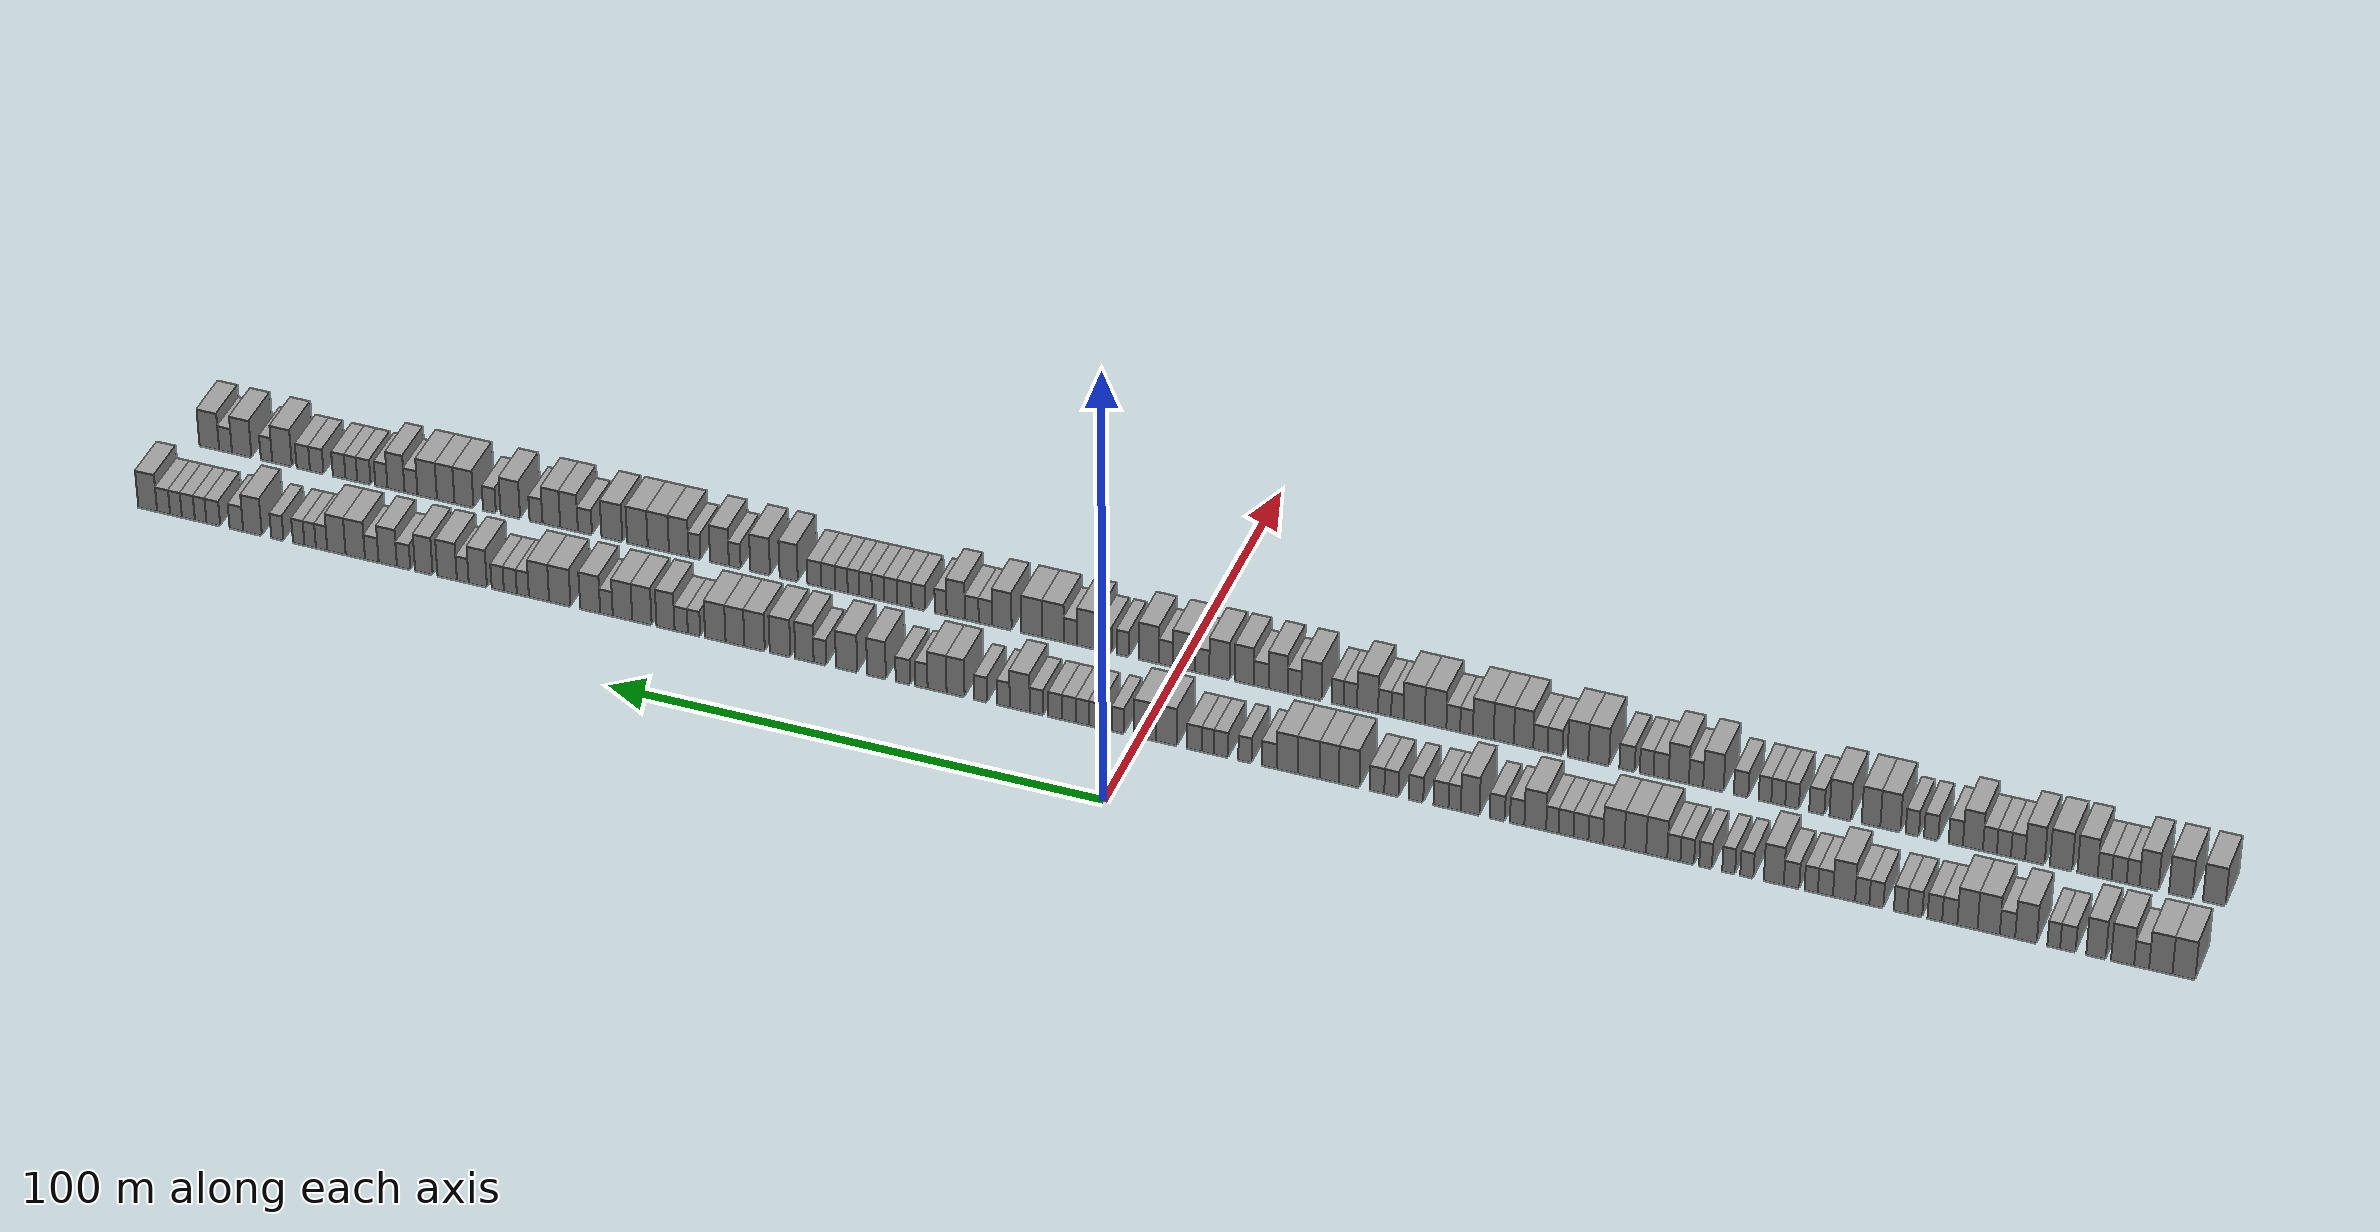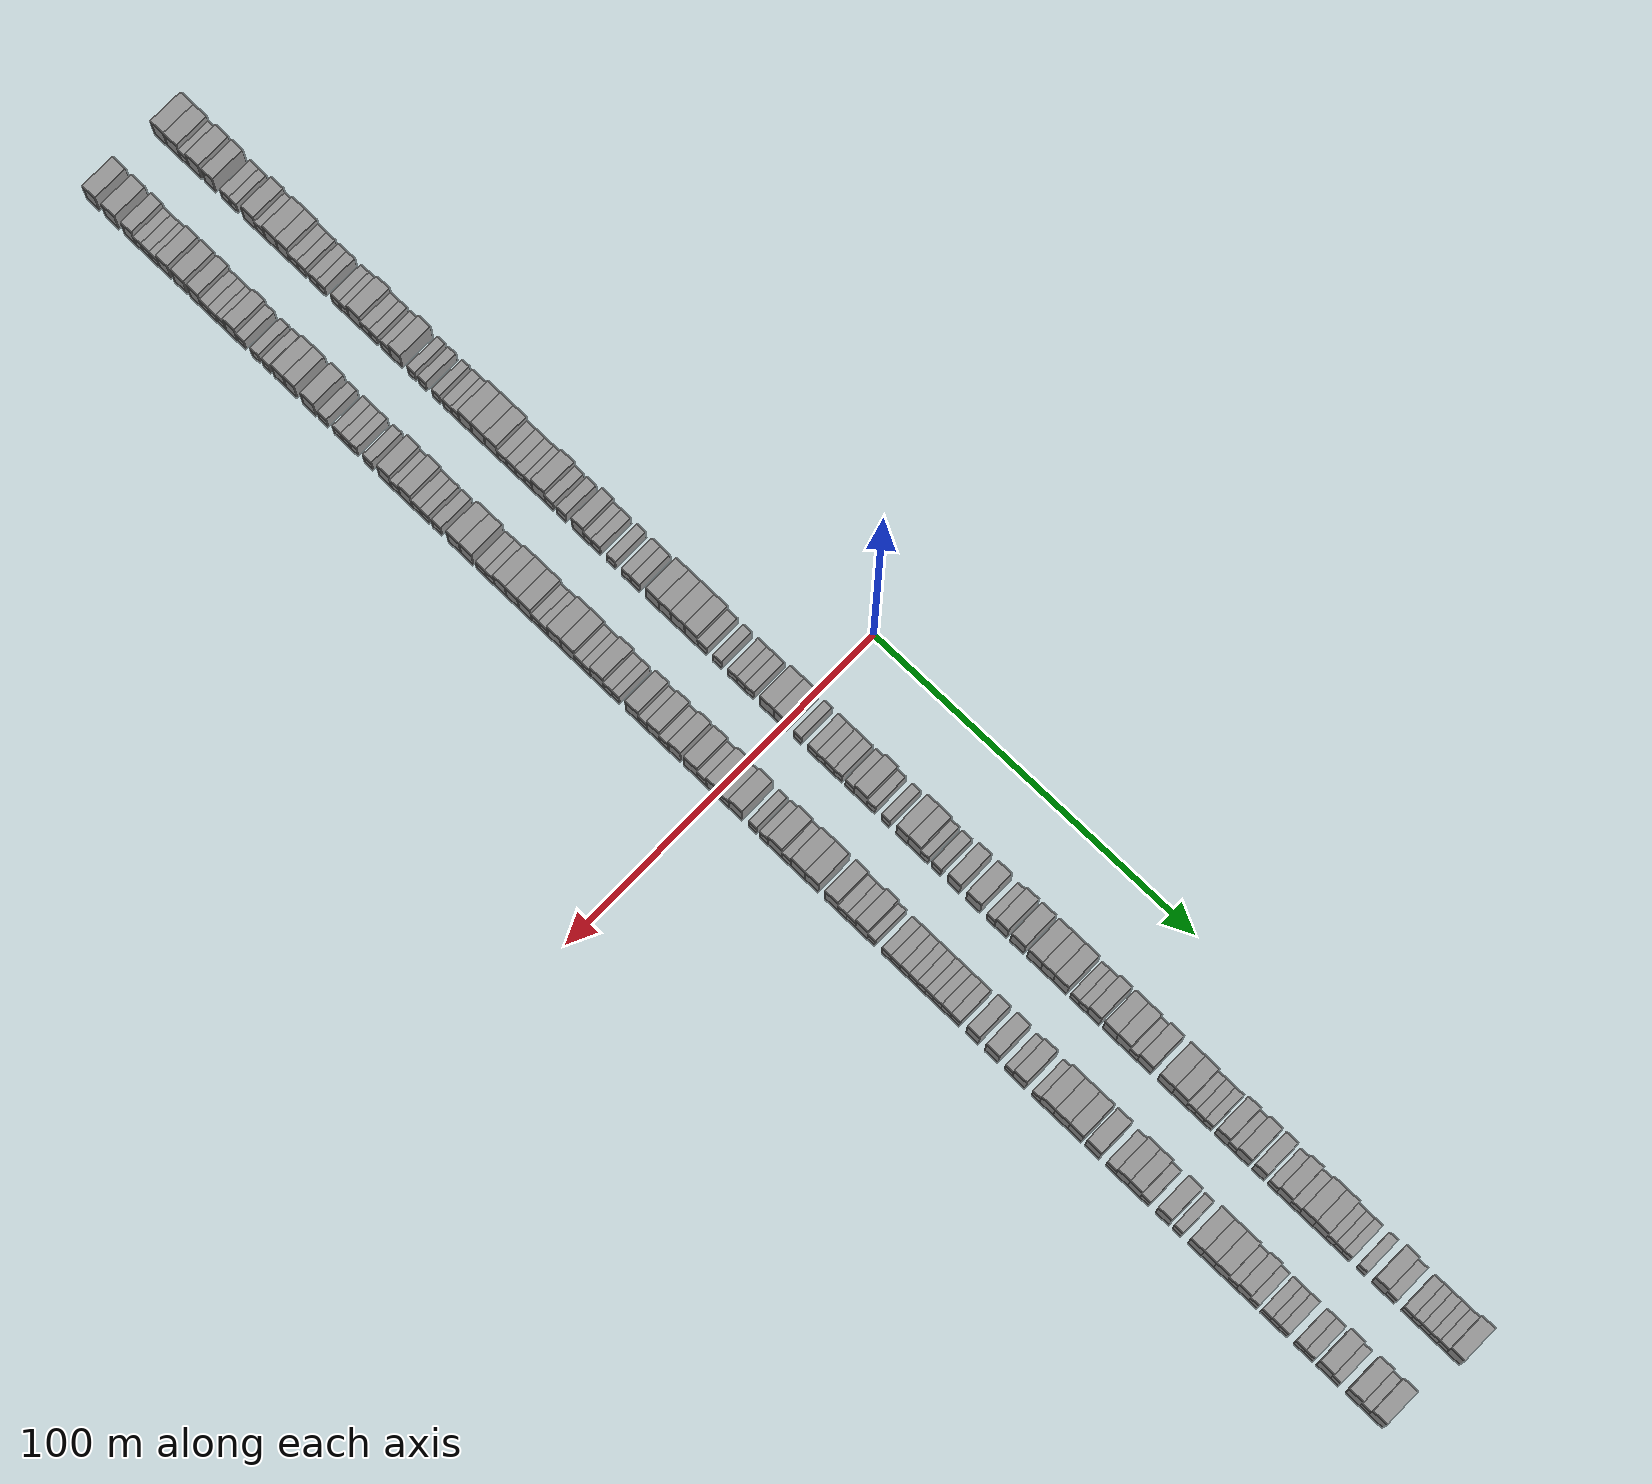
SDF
<sdf version="1.6">
 <world name="default">
  <scene>
   <sky><clouds><speed>12</speed></clouds></sky>
   <ambient>0.4 0.4 0.4 1</ambient>
   <background>0.7 0.7 0.7 1</background>
   <shadows>1</shadows>
  </scene>
  <gravity>0 0 -9.8066</gravity>
  <magnetic_field>6e-06 2.3e-05 -4.2e-05</magnetic_field>
  <physics default="0" name="default_physics" type="ode">
   <ode>
    <solver>
     <type>quick</type>
     <iters>10</iters>
     <sor>1.0</sor>
     <use_dynamic_moi_rescaling>0</use_dynamic_moi_rescaling>
    </solver>
    <constraints>
     <cfm>0</cfm>
     <erp>0.2</erp>
     <contact_max_correcting_vel>100</contact_max_correcting_vel>
     <contact_surface_layer>0.001</contact_surface_layer>
    </constraints>
   </ode>
   <max_step_size>0.004</max_step_size>
   <real_time_factor>1</real_time_factor>
   <real_time_update_rate>250</real_time_update_rate>
  </physics>
  <light name="sun" type="directional">
   <pose>0 0 10 0 0 0</pose>
   <diffuse>0.8 0.8 0.8 1</diffuse>
   <specular>0.2 0.2 0.2 1</specular>
   <attenuation>
    <range>1000</range>
    <constant>0.9</constant>
    <linear>0.01</linear>
    <quadratic>0.001</quadratic>
   </attenuation>
   <direction>-0.5 0.1 -0.9</direction>
  </light>
  <model name="building_1">
   <static>1</static>
   <pose>25.0000 -201.8556 0 0.000000 0.000000 0.000000</pose>
   <link name="link">
    <pose>0 0 4.50 0 0 0</pose>
    <collision name="collision"><geometry><box><size>10.0000 4.2888 9.0000</size></box></geometry></collision>
    <visual name="visual">
     <cast_shadows>0</cast_shadows>
     <geometry><box><size>10.0000 4.2888 9.0000</size></box></geometry>
     <material>
      <script>
       <uri>model://grey_wall/materials/scripts</uri>
       <uri>model://grey_wall/materials/textures</uri>
       <name>vrc/grey_wall</name>
      </script>
     </material>
    </visual>
   </link>
  </model>
  <model name="building_2">
   <static>1</static>
   <pose>25.0000 -197.5242 0 0.000000 0.000000 0.000000</pose>
   <link name="link">
    <pose>0 0 4.50 0 0 0</pose>
    <collision name="collision"><geometry><box><size>10.0000 4.3739 9.0000</size></box></geometry></collision>
    <visual name="visual">
     <cast_shadows>0</cast_shadows>
     <geometry><box><size>10.0000 4.3739 9.0000</size></box></geometry>
     <material>
      <script>
       <uri>model://grey_wall/materials/scripts</uri>
       <uri>model://grey_wall/materials/textures</uri>
       <name>vrc/grey_wall</name>
      </script>
     </material>
    </visual>
   </link>
  </model>
  <model name="building_3">
   <static>1</static>
   <pose>25.0000 -193.9371 0 0.000000 0.000000 0.000000</pose>
   <link name="link">
    <pose>0 0 3.00 0 0 0</pose>
    <collision name="collision"><geometry><box><size>10.0000 2.8003 6.0000</size></box></geometry></collision>
    <visual name="visual">
     <cast_shadows>0</cast_shadows>
     <geometry><box><size>10.0000 2.8003 6.0000</size></box></geometry>
     <material>
      <script>
       <uri>model://grey_wall/materials/scripts</uri>
       <uri>model://grey_wall/materials/textures</uri>
       <name>vrc/grey_wall</name>
      </script>
     </material>
    </visual>
   </link>
  </model>
  <model name="building_4">
   <static>1</static>
   <pose>25.0000 -190.3591 0 0.000000 0.000000 0.000000</pose>
   <link name="link">
    <pose>0 0 4.50 0 0 0</pose>
    <collision name="collision"><geometry><box><size>10.0000 4.3556 9.0000</size></box></geometry></collision>
    <visual name="visual">
     <cast_shadows>0</cast_shadows>
     <geometry><box><size>10.0000 4.3556 9.0000</size></box></geometry>
     <material>
      <script>
       <uri>model://grey_wall/materials/scripts</uri>
       <uri>model://grey_wall/materials/textures</uri>
       <name>vrc/grey_wall</name>
      </script>
     </material>
    </visual>
   </link>
  </model>
  <model name="building_5">
   <static>1</static>
   <pose>25.0000 -185.3532 0 0.000000 0.000000 0.000000</pose>
   <link name="link">
    <pose>0 0 4.50 0 0 0</pose>
    <collision name="collision"><geometry><box><size>10.0000 3.6562 9.0000</size></box></geometry></collision>
    <visual name="visual">
     <cast_shadows>0</cast_shadows>
     <geometry><box><size>10.0000 3.6562 9.0000</size></box></geometry>
     <material>
      <script>
       <uri>model://grey_wall/materials/scripts</uri>
       <uri>model://grey_wall/materials/textures</uri>
       <name>vrc/grey_wall</name>
      </script>
     </material>
    </visual>
   </link>
  </model>
  <model name="building_6">
   <static>1</static>
   <pose>25.0000 -180.0597 0 0.000000 0.000000 0.000000</pose>
   <link name="link">
    <pose>0 0 3.00 0 0 0</pose>
    <collision name="collision"><geometry><box><size>10.0000 2.9308 6.0000</size></box></geometry></collision>
    <visual name="visual">
     <cast_shadows>0</cast_shadows>
     <geometry><box><size>10.0000 2.9308 6.0000</size></box></geometry>
     <material>
      <script>
       <uri>model://grey_wall/materials/scripts</uri>
       <uri>model://grey_wall/materials/textures</uri>
       <name>vrc/grey_wall</name>
      </script>
     </material>
    </visual>
   </link>
  </model>
  <model name="building_7">
   <static>1</static>
   <pose>25.0000 -177.3900 0 0.000000 0.000000 0.000000</pose>
   <link name="link">
    <pose>0 0 3.00 0 0 0</pose>
    <collision name="collision"><geometry><box><size>10.0000 2.4087 6.0000</size></box></geometry></collision>
    <visual name="visual">
     <cast_shadows>0</cast_shadows>
     <geometry><box><size>10.0000 2.4087 6.0000</size></box></geometry>
     <material>
      <script>
       <uri>model://grey_wall/materials/scripts</uri>
       <uri>model://grey_wall/materials/textures</uri>
       <name>vrc/grey_wall</name>
      </script>
     </material>
    </visual>
   </link>
  </model>
  <model name="building_8">
   <static>1</static>
   <pose>25.0000 -172.1442 0 0.000000 0.000000 0.000000</pose>
   <link name="link">
    <pose>0 0 4.50 0 0 0</pose>
    <collision name="collision"><geometry><box><size>10.0000 4.0828 9.0000</size></box></geometry></collision>
    <visual name="visual">
     <cast_shadows>0</cast_shadows>
     <geometry><box><size>10.0000 4.0828 9.0000</size></box></geometry>
     <material>
      <script>
       <uri>model://grey_wall/materials/scripts</uri>
       <uri>model://grey_wall/materials/textures</uri>
       <name>vrc/grey_wall</name>
      </script>
     </material>
    </visual>
   </link>
  </model>
  <model name="building_9">
   <static>1</static>
   <pose>25.0000 -168.6496 0 0.000000 0.000000 0.000000</pose>
   <link name="link">
    <pose>0 0 3.00 0 0 0</pose>
    <collision name="collision"><geometry><box><size>10.0000 2.9065 6.0000</size></box></geometry></collision>
    <visual name="visual">
     <cast_shadows>0</cast_shadows>
     <geometry><box><size>10.0000 2.9065 6.0000</size></box></geometry>
     <material>
      <script>
       <uri>model://grey_wall/materials/scripts</uri>
       <uri>model://grey_wall/materials/textures</uri>
       <name>vrc/grey_wall</name>
      </script>
     </material>
    </visual>
   </link>
  </model>
  <model name="building_10">
   <static>1</static>
   <pose>25.0000 -165.0772 0 0.000000 0.000000 0.000000</pose>
   <link name="link">
    <pose>0 0 4.50 0 0 0</pose>
    <collision name="collision"><geometry><box><size>10.0000 4.2381 9.0000</size></box></geometry></collision>
    <visual name="visual">
     <cast_shadows>0</cast_shadows>
     <geometry><box><size>10.0000 4.2381 9.0000</size></box></geometry>
     <material>
      <script>
       <uri>model://grey_wall/materials/scripts</uri>
       <uri>model://grey_wall/materials/textures</uri>
       <name>vrc/grey_wall</name>
      </script>
     </material>
    </visual>
   </link>
  </model>
  <model name="building_11">
   <static>1</static>
   <pose>25.0000 -161.0481 0 0.000000 0.000000 0.000000</pose>
   <link name="link">
    <pose>0 0 4.50 0 0 0</pose>
    <collision name="collision"><geometry><box><size>10.0000 3.8203 9.0000</size></box></geometry></collision>
    <visual name="visual">
     <cast_shadows>0</cast_shadows>
     <geometry><box><size>10.0000 3.8203 9.0000</size></box></geometry>
     <material>
      <script>
       <uri>model://grey_wall/materials/scripts</uri>
       <uri>model://grey_wall/materials/textures</uri>
       <name>vrc/grey_wall</name>
      </script>
     </material>
    </visual>
   </link>
  </model>
  <model name="building_12">
   <static>1</static>
   <pose>25.0000 -157.6958 0 0.000000 0.000000 0.000000</pose>
   <link name="link">
    <pose>0 0 3.00 0 0 0</pose>
    <collision name="collision"><geometry><box><size>10.0000 2.8843 6.0000</size></box></geometry></collision>
    <visual name="visual">
     <cast_shadows>0</cast_shadows>
     <geometry><box><size>10.0000 2.8843 6.0000</size></box></geometry>
     <material>
      <script>
       <uri>model://grey_wall/materials/scripts</uri>
       <uri>model://grey_wall/materials/textures</uri>
       <name>vrc/grey_wall</name>
      </script>
     </material>
    </visual>
   </link>
  </model>
  <model name="building_13">
   <static>1</static>
   <pose>25.0000 -154.8604 0 0.000000 0.000000 0.000000</pose>
   <link name="link">
    <pose>0 0 3.00 0 0 0</pose>
    <collision name="collision"><geometry><box><size>10.0000 2.7866 6.0000</size></box></geometry></collision>
    <visual name="visual">
     <cast_shadows>0</cast_shadows>
     <geometry><box><size>10.0000 2.7866 6.0000</size></box></geometry>
     <material>
      <script>
       <uri>model://grey_wall/materials/scripts</uri>
       <uri>model://grey_wall/materials/textures</uri>
       <name>vrc/grey_wall</name>
      </script>
     </material>
    </visual>
   </link>
  </model>
  <model name="building_14">
   <static>1</static>
   <pose>25.0000 -151.0621 0 0.000000 0.000000 0.000000</pose>
   <link name="link">
    <pose>0 0 3.00 0 0 0</pose>
    <collision name="collision"><geometry><box><size>10.0000 2.8099 6.0000</size></box></geometry></collision>
    <visual name="visual">
     <cast_shadows>0</cast_shadows>
     <geometry><box><size>10.0000 2.8099 6.0000</size></box></geometry>
     <material>
      <script>
       <uri>model://grey_wall/materials/scripts</uri>
       <uri>model://grey_wall/materials/textures</uri>
       <name>vrc/grey_wall</name>
      </script>
     </material>
    </visual>
   </link>
  </model>
  <model name="building_15">
   <static>1</static>
   <pose>25.0000 -148.3622 0 0.000000 0.000000 0.000000</pose>
   <link name="link">
    <pose>0 0 3.00 0 0 0</pose>
    <collision name="collision"><geometry><box><size>10.0000 2.5898 6.0000</size></box></geometry></collision>
    <visual name="visual">
     <cast_shadows>0</cast_shadows>
     <geometry><box><size>10.0000 2.5898 6.0000</size></box></geometry>
     <material>
      <script>
       <uri>model://grey_wall/materials/scripts</uri>
       <uri>model://grey_wall/materials/textures</uri>
       <name>vrc/grey_wall</name>
      </script>
     </material>
    </visual>
   </link>
  </model>
  <model name="building_16">
   <static>1</static>
   <pose>25.0000 -143.7237 0 0.000000 0.000000 0.000000</pose>
   <link name="link">
    <pose>0 0 3.00 0 0 0</pose>
    <collision name="collision"><geometry><box><size>10.0000 2.6872 6.0000</size></box></geometry></collision>
    <visual name="visual">
     <cast_shadows>0</cast_shadows>
     <geometry><box><size>10.0000 2.6872 6.0000</size></box></geometry>
     <material>
      <script>
       <uri>model://grey_wall/materials/scripts</uri>
       <uri>model://grey_wall/materials/textures</uri>
       <name>vrc/grey_wall</name>
      </script>
     </material>
    </visual>
   </link>
  </model>
  <model name="building_17">
   <static>1</static>
   <pose>25.0000 -141.0242 0 0.000000 0.000000 0.000000</pose>
   <link name="link">
    <pose>0 0 3.00 0 0 0</pose>
    <collision name="collision"><geometry><box><size>10.0000 2.7119 6.0000</size></box></geometry></collision>
    <visual name="visual">
     <cast_shadows>0</cast_shadows>
     <geometry><box><size>10.0000 2.7119 6.0000</size></box></geometry>
     <material>
      <script>
       <uri>model://grey_wall/materials/scripts</uri>
       <uri>model://grey_wall/materials/textures</uri>
       <name>vrc/grey_wall</name>
      </script>
     </material>
    </visual>
   </link>
  </model>
  <model name="building_18">
   <static>1</static>
   <pose>25.0000 -137.5453 0 0.000000 0.000000 0.000000</pose>
   <link name="link">
    <pose>0 0 4.50 0 0 0</pose>
    <collision name="collision"><geometry><box><size>10.0000 4.2459 9.0000</size></box></geometry></collision>
    <visual name="visual">
     <cast_shadows>0</cast_shadows>
     <geometry><box><size>10.0000 4.2459 9.0000</size></box></geometry>
     <material>
      <script>
       <uri>model://grey_wall/materials/scripts</uri>
       <uri>model://grey_wall/materials/textures</uri>
       <name>vrc/grey_wall</name>
      </script>
     </material>
    </visual>
   </link>
  </model>
  <model name="building_19">
   <static>1</static>
   <pose>25.0000 -133.9756 0 0.000000 0.000000 0.000000</pose>
   <link name="link">
    <pose>0 0 3.00 0 0 0</pose>
    <collision name="collision"><geometry><box><size>10.0000 2.8935 6.0000</size></box></geometry></collision>
    <visual name="visual">
     <cast_shadows>0</cast_shadows>
     <geometry><box><size>10.0000 2.8935 6.0000</size></box></geometry>
     <material>
      <script>
       <uri>model://grey_wall/materials/scripts</uri>
       <uri>model://grey_wall/materials/textures</uri>
       <name>vrc/grey_wall</name>
      </script>
     </material>
    </visual>
   </link>
  </model>
  <model name="building_20">
   <static>1</static>
   <pose>25.0000 -131.2498 0 0.000000 0.000000 0.000000</pose>
   <link name="link">
    <pose>0 0 3.00 0 0 0</pose>
    <collision name="collision"><geometry><box><size>10.0000 2.5581 6.0000</size></box></geometry></collision>
    <visual name="visual">
     <cast_shadows>0</cast_shadows>
     <geometry><box><size>10.0000 2.5581 6.0000</size></box></geometry>
     <material>
      <script>
       <uri>model://grey_wall/materials/scripts</uri>
       <uri>model://grey_wall/materials/textures</uri>
       <name>vrc/grey_wall</name>
      </script>
     </material>
    </visual>
   </link>
  </model>
  <model name="building_21">
   <static>1</static>
   <pose>25.0000 -127.4787 0 0.000000 0.000000 0.000000</pose>
   <link name="link">
    <pose>0 0 3.00 0 0 0</pose>
    <collision name="collision"><geometry><box><size>10.0000 2.9840 6.0000</size></box></geometry></collision>
    <visual name="visual">
     <cast_shadows>0</cast_shadows>
     <geometry><box><size>10.0000 2.9840 6.0000</size></box></geometry>
     <material>
      <script>
       <uri>model://grey_wall/materials/scripts</uri>
       <uri>model://grey_wall/materials/textures</uri>
       <name>vrc/grey_wall</name>
      </script>
     </material>
    </visual>
   </link>
  </model>
  <model name="building_22">
   <static>1</static>
   <pose>25.0000 -124.0685 0 0.000000 0.000000 0.000000</pose>
   <link name="link">
    <pose>0 0 4.50 0 0 0</pose>
    <collision name="collision"><geometry><box><size>10.0000 3.8363 9.0000</size></box></geometry></collision>
    <visual name="visual">
     <cast_shadows>0</cast_shadows>
     <geometry><box><size>10.0000 3.8363 9.0000</size></box></geometry>
     <material>
      <script>
       <uri>model://grey_wall/materials/scripts</uri>
       <uri>model://grey_wall/materials/textures</uri>
       <name>vrc/grey_wall</name>
      </script>
     </material>
    </visual>
   </link>
  </model>
  <model name="building_23">
   <static>1</static>
   <pose>25.0000 -118.8895 0 0.000000 0.000000 0.000000</pose>
   <link name="link">
    <pose>0 0 3.00 0 0 0</pose>
    <collision name="collision"><geometry><box><size>10.0000 2.5217 6.0000</size></box></geometry></collision>
    <visual name="visual">
     <cast_shadows>0</cast_shadows>
     <geometry><box><size>10.0000 2.5217 6.0000</size></box></geometry>
     <material>
      <script>
       <uri>model://grey_wall/materials/scripts</uri>
       <uri>model://grey_wall/materials/textures</uri>
       <name>vrc/grey_wall</name>
      </script>
     </material>
    </visual>
   </link>
  </model>
  <model name="building_24">
   <static>1</static>
   <pose>25.0000 -115.3926 0 0.000000 0.000000 0.000000</pose>
   <link name="link">
    <pose>0 0 3.00 0 0 0</pose>
    <collision name="collision"><geometry><box><size>10.0000 2.4723 6.0000</size></box></geometry></collision>
    <visual name="visual">
     <cast_shadows>0</cast_shadows>
     <geometry><box><size>10.0000 2.4723 6.0000</size></box></geometry>
     <material>
      <script>
       <uri>model://grey_wall/materials/scripts</uri>
       <uri>model://grey_wall/materials/textures</uri>
       <name>vrc/grey_wall</name>
      </script>
     </material>
    </visual>
   </link>
  </model>
  <model name="building_25">
   <static>1</static>
   <pose>25.0000 -110.9321 0 0.000000 0.000000 0.000000</pose>
   <link name="link">
    <pose>0 0 3.00 0 0 0</pose>
    <collision name="collision"><geometry><box><size>10.0000 2.4486 6.0000</size></box></geometry></collision>
    <visual name="visual">
     <cast_shadows>0</cast_shadows>
     <geometry><box><size>10.0000 2.4486 6.0000</size></box></geometry>
     <material>
      <script>
       <uri>model://grey_wall/materials/scripts</uri>
       <uri>model://grey_wall/materials/textures</uri>
       <name>vrc/grey_wall</name>
      </script>
     </material>
    </visual>
   </link>
  </model>
  <model name="building_26">
   <static>1</static>
   <pose>25.0000 -107.3968 0 0.000000 0.000000 0.000000</pose>
   <link name="link">
    <pose>0 0 3.00 0 0 0</pose>
    <collision name="collision"><geometry><box><size>10.0000 2.6221 6.0000</size></box></geometry></collision>
    <visual name="visual">
     <cast_shadows>0</cast_shadows>
     <geometry><box><size>10.0000 2.6221 6.0000</size></box></geometry>
     <material>
      <script>
       <uri>model://grey_wall/materials/scripts</uri>
       <uri>model://grey_wall/materials/textures</uri>
       <name>vrc/grey_wall</name>
      </script>
     </material>
    </visual>
   </link>
  </model>
  <model name="building_27">
   <static>1</static>
   <pose>25.0000 -104.8134 0 0.000000 0.000000 0.000000</pose>
   <link name="link">
    <pose>0 0 3.00 0 0 0</pose>
    <collision name="collision"><geometry><box><size>10.0000 2.5448 6.0000</size></box></geometry></collision>
    <visual name="visual">
     <cast_shadows>0</cast_shadows>
     <geometry><box><size>10.0000 2.5448 6.0000</size></box></geometry>
     <material>
      <script>
       <uri>model://grey_wall/materials/scripts</uri>
       <uri>model://grey_wall/materials/textures</uri>
       <name>vrc/grey_wall</name>
      </script>
     </material>
    </visual>
   </link>
  </model>
  <model name="building_28">
   <static>1</static>
   <pose>25.0000 -101.4915 0 0.000000 0.000000 0.000000</pose>
   <link name="link">
    <pose>0 0 4.50 0 0 0</pose>
    <collision name="collision"><geometry><box><size>10.0000 4.0988 9.0000</size></box></geometry></collision>
    <visual name="visual">
     <cast_shadows>0</cast_shadows>
     <geometry><box><size>10.0000 4.0988 9.0000</size></box></geometry>
     <material>
      <script>
       <uri>model://grey_wall/materials/scripts</uri>
       <uri>model://grey_wall/materials/textures</uri>
       <name>vrc/grey_wall</name>
      </script>
     </material>
    </visual>
   </link>
  </model>
  <model name="building_29">
   <static>1</static>
   <pose>25.0000 -97.3312 0 0.000000 0.000000 0.000000</pose>
   <link name="link">
    <pose>0 0 4.50 0 0 0</pose>
    <collision name="collision"><geometry><box><size>10.0000 4.2218 9.0000</size></box></geometry></collision>
    <visual name="visual">
     <cast_shadows>0</cast_shadows>
     <geometry><box><size>10.0000 4.2218 9.0000</size></box></geometry>
     <material>
      <script>
       <uri>model://grey_wall/materials/scripts</uri>
       <uri>model://grey_wall/materials/textures</uri>
       <name>vrc/grey_wall</name>
      </script>
     </material>
    </visual>
   </link>
  </model>
  <model name="building_30">
   <static>1</static>
   <pose>25.0000 -93.1748 0 0.000000 0.000000 0.000000</pose>
   <link name="link">
    <pose>0 0 4.50 0 0 0</pose>
    <collision name="collision"><geometry><box><size>10.0000 4.0911 9.0000</size></box></geometry></collision>
    <visual name="visual">
     <cast_shadows>0</cast_shadows>
     <geometry><box><size>10.0000 4.0911 9.0000</size></box></geometry>
     <material>
      <script>
       <uri>model://grey_wall/materials/scripts</uri>
       <uri>model://grey_wall/materials/textures</uri>
       <name>vrc/grey_wall</name>
      </script>
     </material>
    </visual>
   </link>
  </model>
  <model name="building_31">
   <static>1</static>
   <pose>25.0000 -89.6889 0 0.000000 0.000000 0.000000</pose>
   <link name="link">
    <pose>0 0 3.00 0 0 0</pose>
    <collision name="collision"><geometry><box><size>10.0000 2.8806 6.0000</size></box></geometry></collision>
    <visual name="visual">
     <cast_shadows>0</cast_shadows>
     <geometry><box><size>10.0000 2.8806 6.0000</size></box></geometry>
     <material>
      <script>
       <uri>model://grey_wall/materials/scripts</uri>
       <uri>model://grey_wall/materials/textures</uri>
       <name>vrc/grey_wall</name>
      </script>
     </material>
    </visual>
   </link>
  </model>
  <model name="building_32">
   <static>1</static>
   <pose>25.0000 -86.7943 0 0.000000 0.000000 0.000000</pose>
   <link name="link">
    <pose>0 0 3.00 0 0 0</pose>
    <collision name="collision"><geometry><box><size>10.0000 2.9087 6.0000</size></box></geometry></collision>
    <visual name="visual">
     <cast_shadows>0</cast_shadows>
     <geometry><box><size>10.0000 2.9087 6.0000</size></box></geometry>
     <material>
      <script>
       <uri>model://grey_wall/materials/scripts</uri>
       <uri>model://grey_wall/materials/textures</uri>
       <name>vrc/grey_wall</name>
      </script>
     </material>
    </visual>
   </link>
  </model>
  <model name="building_33">
   <static>1</static>
   <pose>25.0000 -83.8854 0 0.000000 0.000000 0.000000</pose>
   <link name="link">
    <pose>0 0 3.00 0 0 0</pose>
    <collision name="collision"><geometry><box><size>10.0000 2.9092 6.0000</size></box></geometry></collision>
    <visual name="visual">
     <cast_shadows>0</cast_shadows>
     <geometry><box><size>10.0000 2.9092 6.0000</size></box></geometry>
     <material>
      <script>
       <uri>model://grey_wall/materials/scripts</uri>
       <uri>model://grey_wall/materials/textures</uri>
       <name>vrc/grey_wall</name>
      </script>
     </material>
    </visual>
   </link>
  </model>
  <model name="building_34">
   <static>1</static>
   <pose>25.0000 -81.2215 0 0.000000 0.000000 0.000000</pose>
   <link name="link">
    <pose>0 0 3.00 0 0 0</pose>
    <collision name="collision"><geometry><box><size>10.0000 2.4186 6.0000</size></box></geometry></collision>
    <visual name="visual">
     <cast_shadows>0</cast_shadows>
     <geometry><box><size>10.0000 2.4186 6.0000</size></box></geometry>
     <material>
      <script>
       <uri>model://grey_wall/materials/scripts</uri>
       <uri>model://grey_wall/materials/textures</uri>
       <name>vrc/grey_wall</name>
      </script>
     </material>
    </visual>
   </link>
  </model>
  <model name="building_35">
   <static>1</static>
   <pose>25.0000 -77.8905 0 0.000000 0.000000 0.000000</pose>
   <link name="link">
    <pose>0 0 4.50 0 0 0</pose>
    <collision name="collision"><geometry><box><size>10.0000 4.2435 9.0000</size></box></geometry></collision>
    <visual name="visual">
     <cast_shadows>0</cast_shadows>
     <geometry><box><size>10.0000 4.2435 9.0000</size></box></geometry>
     <material>
      <script>
       <uri>model://grey_wall/materials/scripts</uri>
       <uri>model://grey_wall/materials/textures</uri>
       <name>vrc/grey_wall</name>
      </script>
     </material>
    </visual>
   </link>
  </model>
  <model name="building_36">
   <static>1</static>
   <pose>25.0000 -74.3643 0 0.000000 0.000000 0.000000</pose>
   <link name="link">
    <pose>0 0 3.00 0 0 0</pose>
    <collision name="collision"><geometry><box><size>10.0000 2.8089 6.0000</size></box></geometry></collision>
    <visual name="visual">
     <cast_shadows>0</cast_shadows>
     <geometry><box><size>10.0000 2.8089 6.0000</size></box></geometry>
     <material>
      <script>
       <uri>model://grey_wall/materials/scripts</uri>
       <uri>model://grey_wall/materials/textures</uri>
       <name>vrc/grey_wall</name>
      </script>
     </material>
    </visual>
   </link>
  </model>
  <model name="building_37">
   <static>1</static>
   <pose>25.0000 -70.4836 0 0.000000 0.000000 0.000000</pose>
   <link name="link">
    <pose>0 0 3.00 0 0 0</pose>
    <collision name="collision"><geometry><box><size>10.0000 2.9524 6.0000</size></box></geometry></collision>
    <visual name="visual">
     <cast_shadows>0</cast_shadows>
     <geometry><box><size>10.0000 2.9524 6.0000</size></box></geometry>
     <material>
      <script>
       <uri>model://grey_wall/materials/scripts</uri>
       <uri>model://grey_wall/materials/textures</uri>
       <name>vrc/grey_wall</name>
      </script>
     </material>
    </visual>
   </link>
  </model>
  <model name="building_38">
   <static>1</static>
   <pose>25.0000 -65.1776 0 0.000000 0.000000 0.000000</pose>
   <link name="link">
    <pose>0 0 4.50 0 0 0</pose>
    <collision name="collision"><geometry><box><size>10.0000 3.6598 9.0000</size></box></geometry></collision>
    <visual name="visual">
     <cast_shadows>0</cast_shadows>
     <geometry><box><size>10.0000 3.6598 9.0000</size></box></geometry>
     <material>
      <script>
       <uri>model://grey_wall/materials/scripts</uri>
       <uri>model://grey_wall/materials/textures</uri>
       <name>vrc/grey_wall</name>
      </script>
     </material>
    </visual>
   </link>
  </model>
  <model name="building_39">
   <static>1</static>
   <pose>25.0000 -62.1291 0 0.000000 0.000000 0.000000</pose>
   <link name="link">
    <pose>0 0 3.00 0 0 0</pose>
    <collision name="collision"><geometry><box><size>10.0000 2.4372 6.0000</size></box></geometry></collision>
    <visual name="visual">
     <cast_shadows>0</cast_shadows>
     <geometry><box><size>10.0000 2.4372 6.0000</size></box></geometry>
     <material>
      <script>
       <uri>model://grey_wall/materials/scripts</uri>
       <uri>model://grey_wall/materials/textures</uri>
       <name>vrc/grey_wall</name>
      </script>
     </material>
    </visual>
   </link>
  </model>
  <model name="building_40">
   <static>1</static>
   <pose>25.0000 -59.4379 0 0.000000 0.000000 0.000000</pose>
   <link name="link">
    <pose>0 0 3.00 0 0 0</pose>
    <collision name="collision"><geometry><box><size>10.0000 2.9452 6.0000</size></box></geometry></collision>
    <visual name="visual">
     <cast_shadows>0</cast_shadows>
     <geometry><box><size>10.0000 2.9452 6.0000</size></box></geometry>
     <material>
      <script>
       <uri>model://grey_wall/materials/scripts</uri>
       <uri>model://grey_wall/materials/textures</uri>
       <name>vrc/grey_wall</name>
      </script>
     </material>
    </visual>
   </link>
  </model>
  <model name="building_41">
   <static>1</static>
   <pose>25.0000 -54.5569 0 0.000000 0.000000 0.000000</pose>
   <link name="link">
    <pose>0 0 3.00 0 0 0</pose>
    <collision name="collision"><geometry><box><size>10.0000 2.8167 6.0000</size></box></geometry></collision>
    <visual name="visual">
     <cast_shadows>0</cast_shadows>
     <geometry><box><size>10.0000 2.8167 6.0000</size></box></geometry>
     <material>
      <script>
       <uri>model://grey_wall/materials/scripts</uri>
       <uri>model://grey_wall/materials/textures</uri>
       <name>vrc/grey_wall</name>
      </script>
     </material>
    </visual>
   </link>
  </model>
  <model name="building_42">
   <static>1</static>
   <pose>25.0000 -49.7242 0 0.000000 0.000000 0.000000</pose>
   <link name="link">
    <pose>0 0 3.00 0 0 0</pose>
    <collision name="collision"><geometry><box><size>10.0000 2.8488 6.0000</size></box></geometry></collision>
    <visual name="visual">
     <cast_shadows>0</cast_shadows>
     <geometry><box><size>10.0000 2.8488 6.0000</size></box></geometry>
     <material>
      <script>
       <uri>model://grey_wall/materials/scripts</uri>
       <uri>model://grey_wall/materials/textures</uri>
       <name>vrc/grey_wall</name>
      </script>
     </material>
    </visual>
   </link>
  </model>
  <model name="building_43">
   <static>1</static>
   <pose>25.0000 -46.8481 0 0.000000 0.000000 0.000000</pose>
   <link name="link">
    <pose>0 0 3.00 0 0 0</pose>
    <collision name="collision"><geometry><box><size>10.0000 2.9032 6.0000</size></box></geometry></collision>
    <visual name="visual">
     <cast_shadows>0</cast_shadows>
     <geometry><box><size>10.0000 2.9032 6.0000</size></box></geometry>
     <material>
      <script>
       <uri>model://grey_wall/materials/scripts</uri>
       <uri>model://grey_wall/materials/textures</uri>
       <name>vrc/grey_wall</name>
      </script>
     </material>
    </visual>
   </link>
  </model>
  <model name="building_44">
   <static>1</static>
   <pose>25.0000 -41.3702 0 0.000000 0.000000 0.000000</pose>
   <link name="link">
    <pose>0 0 4.50 0 0 0</pose>
    <collision name="collision"><geometry><box><size>10.0000 4.0526 9.0000</size></box></geometry></collision>
    <visual name="visual">
     <cast_shadows>0</cast_shadows>
     <geometry><box><size>10.0000 4.0526 9.0000</size></box></geometry>
     <material>
      <script>
       <uri>model://grey_wall/materials/scripts</uri>
       <uri>model://grey_wall/materials/textures</uri>
       <name>vrc/grey_wall</name>
      </script>
     </material>
    </visual>
   </link>
  </model>
  <model name="building_45">
   <static>1</static>
   <pose>25.0000 -37.4439 0 0.000000 0.000000 0.000000</pose>
   <link name="link">
    <pose>0 0 4.50 0 0 0</pose>
    <collision name="collision"><geometry><box><size>10.0000 3.8000 9.0000</size></box></geometry></collision>
    <visual name="visual">
     <cast_shadows>0</cast_shadows>
     <geometry><box><size>10.0000 3.8000 9.0000</size></box></geometry>
     <material>
      <script>
       <uri>model://grey_wall/materials/scripts</uri>
       <uri>model://grey_wall/materials/textures</uri>
       <name>vrc/grey_wall</name>
      </script>
     </material>
    </visual>
   </link>
  </model>
  <model name="building_46">
   <static>1</static>
   <pose>25.0000 -33.3550 0 0.000000 0.000000 0.000000</pose>
   <link name="link">
    <pose>0 0 4.50 0 0 0</pose>
    <collision name="collision"><geometry><box><size>10.0000 4.3778 9.0000</size></box></geometry></collision>
    <visual name="visual">
     <cast_shadows>0</cast_shadows>
     <geometry><box><size>10.0000 4.3778 9.0000</size></box></geometry>
     <material>
      <script>
       <uri>model://grey_wall/materials/scripts</uri>
       <uri>model://grey_wall/materials/textures</uri>
       <name>vrc/grey_wall</name>
      </script>
     </material>
    </visual>
   </link>
  </model>
  <model name="building_47">
   <static>1</static>
   <pose>25.0000 -29.0945 0 0.000000 0.000000 0.000000</pose>
   <link name="link">
    <pose>0 0 4.50 0 0 0</pose>
    <collision name="collision"><geometry><box><size>10.0000 4.1430 9.0000</size></box></geometry></collision>
    <visual name="visual">
     <cast_shadows>0</cast_shadows>
     <geometry><box><size>10.0000 4.1430 9.0000</size></box></geometry>
     <material>
      <script>
       <uri>model://grey_wall/materials/scripts</uri>
       <uri>model://grey_wall/materials/textures</uri>
       <name>vrc/grey_wall</name>
      </script>
     </material>
    </visual>
   </link>
  </model>
  <model name="building_48">
   <static>1</static>
   <pose>25.0000 -25.5393 0 0.000000 0.000000 0.000000</pose>
   <link name="link">
    <pose>0 0 3.00 0 0 0</pose>
    <collision name="collision"><geometry><box><size>10.0000 2.9674 6.0000</size></box></geometry></collision>
    <visual name="visual">
     <cast_shadows>0</cast_shadows>
     <geometry><box><size>10.0000 2.9674 6.0000</size></box></geometry>
     <material>
      <script>
       <uri>model://grey_wall/materials/scripts</uri>
       <uri>model://grey_wall/materials/textures</uri>
       <name>vrc/grey_wall</name>
      </script>
     </material>
    </visual>
   </link>
  </model>
  <model name="building_49">
   <static>1</static>
   <pose>25.0000 -20.7323 0 0.000000 0.000000 0.000000</pose>
   <link name="link">
    <pose>0 0 3.00 0 0 0</pose>
    <collision name="collision"><geometry><box><size>10.0000 2.6467 6.0000</size></box></geometry></collision>
    <visual name="visual">
     <cast_shadows>0</cast_shadows>
     <geometry><box><size>10.0000 2.6467 6.0000</size></box></geometry>
     <material>
      <script>
       <uri>model://grey_wall/materials/scripts</uri>
       <uri>model://grey_wall/materials/textures</uri>
       <name>vrc/grey_wall</name>
      </script>
     </material>
    </visual>
   </link>
  </model>
  <model name="building_50">
   <static>1</static>
   <pose>25.0000 -16.0155 0 0.000000 0.000000 0.000000</pose>
   <link name="link">
    <pose>0 0 3.00 0 0 0</pose>
    <collision name="collision"><geometry><box><size>10.0000 2.7867 6.0000</size></box></geometry></collision>
    <visual name="visual">
     <cast_shadows>0</cast_shadows>
     <geometry><box><size>10.0000 2.7867 6.0000</size></box></geometry>
     <material>
      <script>
       <uri>model://grey_wall/materials/scripts</uri>
       <uri>model://grey_wall/materials/textures</uri>
       <name>vrc/grey_wall</name>
      </script>
     </material>
    </visual>
   </link>
  </model>
  <model name="building_51">
   <static>1</static>
   <pose>25.0000 -13.3936 0 0.000000 0.000000 0.000000</pose>
   <link name="link">
    <pose>0 0 3.00 0 0 0</pose>
    <collision name="collision"><geometry><box><size>10.0000 2.4571 6.0000</size></box></geometry></collision>
    <visual name="visual">
     <cast_shadows>0</cast_shadows>
     <geometry><box><size>10.0000 2.4571 6.0000</size></box></geometry>
     <material>
      <script>
       <uri>model://grey_wall/materials/scripts</uri>
       <uri>model://grey_wall/materials/textures</uri>
       <name>vrc/grey_wall</name>
      </script>
     </material>
    </visual>
   </link>
  </model>
  <model name="building_52">
   <static>1</static>
   <pose>25.0000 -10.6861 0 0.000000 0.000000 0.000000</pose>
   <link name="link">
    <pose>0 0 3.00 0 0 0</pose>
    <collision name="collision"><geometry><box><size>10.0000 2.9580 6.0000</size></box></geometry></collision>
    <visual name="visual">
     <cast_shadows>0</cast_shadows>
     <geometry><box><size>10.0000 2.9580 6.0000</size></box></geometry>
     <material>
      <script>
       <uri>model://grey_wall/materials/scripts</uri>
       <uri>model://grey_wall/materials/textures</uri>
       <name>vrc/grey_wall</name>
      </script>
     </material>
    </visual>
   </link>
  </model>
  <model name="building_53">
   <static>1</static>
   <pose>25.0000 -5.0630 0 0.000000 0.000000 0.000000</pose>
   <link name="link">
    <pose>0 0 4.50 0 0 0</pose>
    <collision name="collision"><geometry><box><size>10.0000 4.2881 9.0000</size></box></geometry></collision>
    <visual name="visual">
     <cast_shadows>0</cast_shadows>
     <geometry><box><size>10.0000 4.2881 9.0000</size></box></geometry>
     <material>
      <script>
       <uri>model://grey_wall/materials/scripts</uri>
       <uri>model://grey_wall/materials/textures</uri>
       <name>vrc/grey_wall</name>
      </script>
     </material>
    </visual>
   </link>
  </model>
  <model name="building_54">
   <static>1</static>
   <pose>25.0000 -0.7715 0 0.000000 0.000000 0.000000</pose>
   <link name="link">
    <pose>0 0 4.50 0 0 0</pose>
    <collision name="collision"><geometry><box><size>10.0000 4.2949 9.0000</size></box></geometry></collision>
    <visual name="visual">
     <cast_shadows>0</cast_shadows>
     <geometry><box><size>10.0000 4.2949 9.0000</size></box></geometry>
     <material>
      <script>
       <uri>model://grey_wall/materials/scripts</uri>
       <uri>model://grey_wall/materials/textures</uri>
       <name>vrc/grey_wall</name>
      </script>
     </material>
    </visual>
   </link>
  </model>
  <model name="building_55">
   <static>1</static>
   <pose>25.0000 4.6251 0 0.000000 0.000000 0.000000</pose>
   <link name="link">
    <pose>0 0 3.00 0 0 0</pose>
    <collision name="collision"><geometry><box><size>10.0000 2.4984 6.0000</size></box></geometry></collision>
    <visual name="visual">
     <cast_shadows>0</cast_shadows>
     <geometry><box><size>10.0000 2.4984 6.0000</size></box></geometry>
     <material>
      <script>
       <uri>model://grey_wall/materials/scripts</uri>
       <uri>model://grey_wall/materials/textures</uri>
       <name>vrc/grey_wall</name>
      </script>
     </material>
    </visual>
   </link>
  </model>
  <model name="building_56">
   <static>1</static>
   <pose>25.0000 9.1985 0 0.000000 0.000000 0.000000</pose>
   <link name="link">
    <pose>0 0 3.00 0 0 0</pose>
    <collision name="collision"><geometry><box><size>10.0000 2.6484 6.0000</size></box></geometry></collision>
    <visual name="visual">
     <cast_shadows>0</cast_shadows>
     <geometry><box><size>10.0000 2.6484 6.0000</size></box></geometry>
     <material>
      <script>
       <uri>model://grey_wall/materials/scripts</uri>
       <uri>model://grey_wall/materials/textures</uri>
       <name>vrc/grey_wall</name>
      </script>
     </material>
    </visual>
   </link>
  </model>
  <model name="building_57">
   <static>1</static>
   <pose>25.0000 11.7842 0 0.000000 0.000000 0.000000</pose>
   <link name="link">
    <pose>0 0 3.00 0 0 0</pose>
    <collision name="collision"><geometry><box><size>10.0000 2.5229 6.0000</size></box></geometry></collision>
    <visual name="visual">
     <cast_shadows>0</cast_shadows>
     <geometry><box><size>10.0000 2.5229 6.0000</size></box></geometry>
     <material>
      <script>
       <uri>model://grey_wall/materials/scripts</uri>
       <uri>model://grey_wall/materials/textures</uri>
       <name>vrc/grey_wall</name>
      </script>
     </material>
    </visual>
   </link>
  </model>
  <model name="building_58">
   <static>1</static>
   <pose>25.0000 14.4727 0 0.000000 0.000000 0.000000</pose>
   <link name="link">
    <pose>0 0 3.00 0 0 0</pose>
    <collision name="collision"><geometry><box><size>10.0000 2.8541 6.0000</size></box></geometry></collision>
    <visual name="visual">
     <cast_shadows>0</cast_shadows>
     <geometry><box><size>10.0000 2.8541 6.0000</size></box></geometry>
     <material>
      <script>
       <uri>model://grey_wall/materials/scripts</uri>
       <uri>model://grey_wall/materials/textures</uri>
       <name>vrc/grey_wall</name>
      </script>
     </material>
    </visual>
   </link>
  </model>
  <model name="building_59">
   <static>1</static>
   <pose>25.0000 17.2530 0 0.000000 0.000000 0.000000</pose>
   <link name="link">
    <pose>0 0 3.00 0 0 0</pose>
    <collision name="collision"><geometry><box><size>10.0000 2.7065 6.0000</size></box></geometry></collision>
    <visual name="visual">
     <cast_shadows>0</cast_shadows>
     <geometry><box><size>10.0000 2.7065 6.0000</size></box></geometry>
     <material>
      <script>
       <uri>model://grey_wall/materials/scripts</uri>
       <uri>model://grey_wall/materials/textures</uri>
       <name>vrc/grey_wall</name>
      </script>
     </material>
    </visual>
   </link>
  </model>
  <model name="building_60">
   <static>1</static>
   <pose>25.0000 20.9910 0 0.000000 0.000000 0.000000</pose>
   <link name="link">
    <pose>0 0 3.00 0 0 0</pose>
    <collision name="collision"><geometry><box><size>10.0000 2.7695 6.0000</size></box></geometry></collision>
    <visual name="visual">
     <cast_shadows>0</cast_shadows>
     <geometry><box><size>10.0000 2.7695 6.0000</size></box></geometry>
     <material>
      <script>
       <uri>model://grey_wall/materials/scripts</uri>
       <uri>model://grey_wall/materials/textures</uri>
       <name>vrc/grey_wall</name>
      </script>
     </material>
    </visual>
   </link>
  </model>
  <model name="building_61">
   <static>1</static>
   <pose>25.0000 24.3944 0 0.000000 0.000000 0.000000</pose>
   <link name="link">
    <pose>0 0 4.50 0 0 0</pose>
    <collision name="collision"><geometry><box><size>10.0000 4.0373 9.0000</size></box></geometry></collision>
    <visual name="visual">
     <cast_shadows>0</cast_shadows>
     <geometry><box><size>10.0000 4.0373 9.0000</size></box></geometry>
     <material>
      <script>
       <uri>model://grey_wall/materials/scripts</uri>
       <uri>model://grey_wall/materials/textures</uri>
       <name>vrc/grey_wall</name>
      </script>
     </material>
    </visual>
   </link>
  </model>
  <model name="building_62">
   <static>1</static>
   <pose>25.0000 27.6877 0 0.000000 0.000000 0.000000</pose>
   <link name="link">
    <pose>0 0 3.00 0 0 0</pose>
    <collision name="collision"><geometry><box><size>10.0000 2.5493 6.0000</size></box></geometry></collision>
    <visual name="visual">
     <cast_shadows>0</cast_shadows>
     <geometry><box><size>10.0000 2.5493 6.0000</size></box></geometry>
     <material>
      <script>
       <uri>model://grey_wall/materials/scripts</uri>
       <uri>model://grey_wall/materials/textures</uri>
       <name>vrc/grey_wall</name>
      </script>
     </material>
    </visual>
   </link>
  </model>
  <model name="building_63">
   <static>1</static>
   <pose>25.0000 32.2560 0 0.000000 0.000000 0.000000</pose>
   <link name="link">
    <pose>0 0 3.00 0 0 0</pose>
    <collision name="collision"><geometry><box><size>10.0000 2.5872 6.0000</size></box></geometry></collision>
    <visual name="visual">
     <cast_shadows>0</cast_shadows>
     <geometry><box><size>10.0000 2.5872 6.0000</size></box></geometry>
     <material>
      <script>
       <uri>model://grey_wall/materials/scripts</uri>
       <uri>model://grey_wall/materials/textures</uri>
       <name>vrc/grey_wall</name>
      </script>
     </material>
    </visual>
   </link>
  </model>
  <model name="building_64">
   <static>1</static>
   <pose>25.0000 37.3747 0 0.000000 0.000000 0.000000</pose>
   <link name="link">
    <pose>0 0 4.50 0 0 0</pose>
    <collision name="collision"><geometry><box><size>10.0000 3.6503 9.0000</size></box></geometry></collision>
    <visual name="visual">
     <cast_shadows>0</cast_shadows>
     <geometry><box><size>10.0000 3.6503 9.0000</size></box></geometry>
     <material>
      <script>
       <uri>model://grey_wall/materials/scripts</uri>
       <uri>model://grey_wall/materials/textures</uri>
       <name>vrc/grey_wall</name>
      </script>
     </material>
    </visual>
   </link>
  </model>
  <model name="building_65">
   <static>1</static>
   <pose>25.0000 41.1248 0 0.000000 0.000000 0.000000</pose>
   <link name="link">
    <pose>0 0 4.50 0 0 0</pose>
    <collision name="collision"><geometry><box><size>10.0000 3.8499 9.0000</size></box></geometry></collision>
    <visual name="visual">
     <cast_shadows>0</cast_shadows>
     <geometry><box><size>10.0000 3.8499 9.0000</size></box></geometry>
     <material>
      <script>
       <uri>model://grey_wall/materials/scripts</uri>
       <uri>model://grey_wall/materials/textures</uri>
       <name>vrc/grey_wall</name>
      </script>
     </material>
    </visual>
   </link>
  </model>
  <model name="building_66">
   <static>1</static>
   <pose>25.0000 44.2967 0 0.000000 0.000000 0.000000</pose>
   <link name="link">
    <pose>0 0 3.00 0 0 0</pose>
    <collision name="collision"><geometry><box><size>10.0000 2.4941 6.0000</size></box></geometry></collision>
    <visual name="visual">
     <cast_shadows>0</cast_shadows>
     <geometry><box><size>10.0000 2.4941 6.0000</size></box></geometry>
     <material>
      <script>
       <uri>model://grey_wall/materials/scripts</uri>
       <uri>model://grey_wall/materials/textures</uri>
       <name>vrc/grey_wall</name>
      </script>
     </material>
    </visual>
   </link>
  </model>
  <model name="building_67">
   <static>1</static>
   <pose>25.0000 48.0324 0 0.000000 0.000000 0.000000</pose>
   <link name="link">
    <pose>0 0 3.00 0 0 0</pose>
    <collision name="collision"><geometry><box><size>10.0000 2.9772 6.0000</size></box></geometry></collision>
    <visual name="visual">
     <cast_shadows>0</cast_shadows>
     <geometry><box><size>10.0000 2.9772 6.0000</size></box></geometry>
     <material>
      <script>
       <uri>model://grey_wall/materials/scripts</uri>
       <uri>model://grey_wall/materials/textures</uri>
       <name>vrc/grey_wall</name>
      </script>
     </material>
    </visual>
   </link>
  </model>
  <model name="building_68">
   <static>1</static>
   <pose>25.0000 53.4341 0 0.000000 0.000000 0.000000</pose>
   <link name="link">
    <pose>0 0 4.50 0 0 0</pose>
    <collision name="collision"><geometry><box><size>10.0000 3.8263 9.0000</size></box></geometry></collision>
    <visual name="visual">
     <cast_shadows>0</cast_shadows>
     <geometry><box><size>10.0000 3.8263 9.0000</size></box></geometry>
     <material>
      <script>
       <uri>model://grey_wall/materials/scripts</uri>
       <uri>model://grey_wall/materials/textures</uri>
       <name>vrc/grey_wall</name>
      </script>
     </material>
    </visual>
   </link>
  </model>
  <model name="building_69">
   <static>1</static>
   <pose>25.0000 59.5182 0 0.000000 0.000000 0.000000</pose>
   <link name="link">
    <pose>0 0 4.50 0 0 0</pose>
    <collision name="collision"><geometry><box><size>10.0000 4.3419 9.0000</size></box></geometry></collision>
    <visual name="visual">
     <cast_shadows>0</cast_shadows>
     <geometry><box><size>10.0000 4.3419 9.0000</size></box></geometry>
     <material>
      <script>
       <uri>model://grey_wall/materials/scripts</uri>
       <uri>model://grey_wall/materials/textures</uri>
       <name>vrc/grey_wall</name>
      </script>
     </material>
    </visual>
   </link>
  </model>
  <model name="building_70">
   <static>1</static>
   <pose>25.0000 64.9756 0 0.000000 0.000000 0.000000</pose>
   <link name="link">
    <pose>0 0 3.00 0 0 0</pose>
    <collision name="collision"><geometry><box><size>10.0000 2.5729 6.0000</size></box></geometry></collision>
    <visual name="visual">
     <cast_shadows>0</cast_shadows>
     <geometry><box><size>10.0000 2.5729 6.0000</size></box></geometry>
     <material>
      <script>
       <uri>model://grey_wall/materials/scripts</uri>
       <uri>model://grey_wall/materials/textures</uri>
       <name>vrc/grey_wall</name>
      </script>
     </material>
    </visual>
   </link>
  </model>
  <model name="building_71">
   <static>1</static>
   <pose>25.0000 68.1362 0 0.000000 0.000000 0.000000</pose>
   <link name="link">
    <pose>0 0 4.50 0 0 0</pose>
    <collision name="collision"><geometry><box><size>10.0000 3.7482 9.0000</size></box></geometry></collision>
    <visual name="visual">
     <cast_shadows>0</cast_shadows>
     <geometry><box><size>10.0000 3.7482 9.0000</size></box></geometry>
     <material>
      <script>
       <uri>model://grey_wall/materials/scripts</uri>
       <uri>model://grey_wall/materials/textures</uri>
       <name>vrc/grey_wall</name>
      </script>
     </material>
    </visual>
   </link>
  </model>
  <model name="building_72">
   <static>1</static>
   <pose>25.0000 73.1373 0 0.000000 0.000000 0.000000</pose>
   <link name="link">
    <pose>0 0 4.50 0 0 0</pose>
    <collision name="collision"><geometry><box><size>10.0000 4.2538 9.0000</size></box></geometry></collision>
    <visual name="visual">
     <cast_shadows>0</cast_shadows>
     <geometry><box><size>10.0000 4.2538 9.0000</size></box></geometry>
     <material>
      <script>
       <uri>model://grey_wall/materials/scripts</uri>
       <uri>model://grey_wall/materials/textures</uri>
       <name>vrc/grey_wall</name>
      </script>
     </material>
    </visual>
   </link>
  </model>
  <model name="building_73">
   <static>1</static>
   <pose>25.0000 78.3566 0 0.000000 0.000000 0.000000</pose>
   <link name="link">
    <pose>0 0 4.50 0 0 0</pose>
    <collision name="collision"><geometry><box><size>10.0000 4.1849 9.0000</size></box></geometry></collision>
    <visual name="visual">
     <cast_shadows>0</cast_shadows>
     <geometry><box><size>10.0000 4.1849 9.0000</size></box></geometry>
     <material>
      <script>
       <uri>model://grey_wall/materials/scripts</uri>
       <uri>model://grey_wall/materials/textures</uri>
       <name>vrc/grey_wall</name>
      </script>
     </material>
    </visual>
   </link>
  </model>
  <model name="building_74">
   <static>1</static>
   <pose>25.0000 82.3882 0 0.000000 0.000000 0.000000</pose>
   <link name="link">
    <pose>0 0 4.50 0 0 0</pose>
    <collision name="collision"><geometry><box><size>10.0000 3.8783 9.0000</size></box></geometry></collision>
    <visual name="visual">
     <cast_shadows>0</cast_shadows>
     <geometry><box><size>10.0000 3.8783 9.0000</size></box></geometry>
     <material>
      <script>
       <uri>model://grey_wall/materials/scripts</uri>
       <uri>model://grey_wall/materials/textures</uri>
       <name>vrc/grey_wall</name>
      </script>
     </material>
    </visual>
   </link>
  </model>
  <model name="building_75">
   <static>1</static>
   <pose>25.0000 86.4307 0 0.000000 0.000000 0.000000</pose>
   <link name="link">
    <pose>0 0 4.50 0 0 0</pose>
    <collision name="collision"><geometry><box><size>10.0000 4.2067 9.0000</size></box></geometry></collision>
    <visual name="visual">
     <cast_shadows>0</cast_shadows>
     <geometry><box><size>10.0000 4.2067 9.0000</size></box></geometry>
     <material>
      <script>
       <uri>model://grey_wall/materials/scripts</uri>
       <uri>model://grey_wall/materials/textures</uri>
       <name>vrc/grey_wall</name>
      </script>
     </material>
    </visual>
   </link>
  </model>
  <model name="building_76">
   <static>1</static>
   <pose>25.0000 90.8180 0 0.000000 0.000000 0.000000</pose>
   <link name="link">
    <pose>0 0 3.00 0 0 0</pose>
    <collision name="collision"><geometry><box><size>10.0000 2.5678 6.0000</size></box></geometry></collision>
    <visual name="visual">
     <cast_shadows>0</cast_shadows>
     <geometry><box><size>10.0000 2.5678 6.0000</size></box></geometry>
     <material>
      <script>
       <uri>model://grey_wall/materials/scripts</uri>
       <uri>model://grey_wall/materials/textures</uri>
       <name>vrc/grey_wall</name>
      </script>
     </material>
    </visual>
   </link>
  </model>
  <model name="building_77">
   <static>1</static>
   <pose>25.0000 93.4687 0 0.000000 0.000000 0.000000</pose>
   <link name="link">
    <pose>0 0 3.00 0 0 0</pose>
    <collision name="collision"><geometry><box><size>10.0000 2.7337 6.0000</size></box></geometry></collision>
    <visual name="visual">
     <cast_shadows>0</cast_shadows>
     <geometry><box><size>10.0000 2.7337 6.0000</size></box></geometry>
     <material>
      <script>
       <uri>model://grey_wall/materials/scripts</uri>
       <uri>model://grey_wall/materials/textures</uri>
       <name>vrc/grey_wall</name>
      </script>
     </material>
    </visual>
   </link>
  </model>
  <model name="building_78">
   <static>1</static>
   <pose>25.0000 96.7047 0 0.000000 0.000000 0.000000</pose>
   <link name="link">
    <pose>0 0 4.50 0 0 0</pose>
    <collision name="collision"><geometry><box><size>10.0000 3.7382 9.0000</size></box></geometry></collision>
    <visual name="visual">
     <cast_shadows>0</cast_shadows>
     <geometry><box><size>10.0000 3.7382 9.0000</size></box></geometry>
     <material>
      <script>
       <uri>model://grey_wall/materials/scripts</uri>
       <uri>model://grey_wall/materials/textures</uri>
       <name>vrc/grey_wall</name>
      </script>
     </material>
    </visual>
   </link>
  </model>
  <model name="building_79">
   <static>1</static>
   <pose>25.0000 101.5788 0 0.000000 0.000000 0.000000</pose>
   <link name="link">
    <pose>0 0 4.50 0 0 0</pose>
    <collision name="collision"><geometry><box><size>10.0000 4.0099 9.0000</size></box></geometry></collision>
    <visual name="visual">
     <cast_shadows>0</cast_shadows>
     <geometry><box><size>10.0000 4.0099 9.0000</size></box></geometry>
     <material>
      <script>
       <uri>model://grey_wall/materials/scripts</uri>
       <uri>model://grey_wall/materials/textures</uri>
       <name>vrc/grey_wall</name>
      </script>
     </material>
    </visual>
   </link>
  </model>
  <model name="building_80">
   <static>1</static>
   <pose>25.0000 105.6009 0 0.000000 0.000000 0.000000</pose>
   <link name="link">
    <pose>0 0 4.50 0 0 0</pose>
    <collision name="collision"><geometry><box><size>10.0000 4.0342 9.0000</size></box></geometry></collision>
    <visual name="visual">
     <cast_shadows>0</cast_shadows>
     <geometry><box><size>10.0000 4.0342 9.0000</size></box></geometry>
     <material>
      <script>
       <uri>model://grey_wall/materials/scripts</uri>
       <uri>model://grey_wall/materials/textures</uri>
       <name>vrc/grey_wall</name>
      </script>
     </material>
    </visual>
   </link>
  </model>
  <model name="building_81">
   <static>1</static>
   <pose>25.0000 108.9214 0 0.000000 0.000000 0.000000</pose>
   <link name="link">
    <pose>0 0 3.00 0 0 0</pose>
    <collision name="collision"><geometry><box><size>10.0000 2.6068 6.0000</size></box></geometry></collision>
    <visual name="visual">
     <cast_shadows>0</cast_shadows>
     <geometry><box><size>10.0000 2.6068 6.0000</size></box></geometry>
     <material>
      <script>
       <uri>model://grey_wall/materials/scripts</uri>
       <uri>model://grey_wall/materials/textures</uri>
       <name>vrc/grey_wall</name>
      </script>
     </material>
    </visual>
   </link>
  </model>
  <model name="building_82">
   <static>1</static>
   <pose>25.0000 112.3044 0 0.000000 0.000000 0.000000</pose>
   <link name="link">
    <pose>0 0 4.50 0 0 0</pose>
    <collision name="collision"><geometry><box><size>10.0000 4.1591 9.0000</size></box></geometry></collision>
    <visual name="visual">
     <cast_shadows>0</cast_shadows>
     <geometry><box><size>10.0000 4.1591 9.0000</size></box></geometry>
     <material>
      <script>
       <uri>model://grey_wall/materials/scripts</uri>
       <uri>model://grey_wall/materials/textures</uri>
       <name>vrc/grey_wall</name>
      </script>
     </material>
    </visual>
   </link>
  </model>
  <model name="building_83">
   <static>1</static>
   <pose>25.0000 118.6127 0 0.000000 0.000000 0.000000</pose>
   <link name="link">
    <pose>0 0 4.50 0 0 0</pose>
    <collision name="collision"><geometry><box><size>10.0000 4.4575 9.0000</size></box></geometry></collision>
    <visual name="visual">
     <cast_shadows>0</cast_shadows>
     <geometry><box><size>10.0000 4.4575 9.0000</size></box></geometry>
     <material>
      <script>
       <uri>model://grey_wall/materials/scripts</uri>
       <uri>model://grey_wall/materials/textures</uri>
       <name>vrc/grey_wall</name>
      </script>
     </material>
    </visual>
   </link>
  </model>
  <model name="building_84">
   <static>1</static>
   <pose>25.0000 122.9503 0 0.000000 0.000000 0.000000</pose>
   <link name="link">
    <pose>0 0 4.50 0 0 0</pose>
    <collision name="collision"><geometry><box><size>10.0000 4.2178 9.0000</size></box></geometry></collision>
    <visual name="visual">
     <cast_shadows>0</cast_shadows>
     <geometry><box><size>10.0000 4.2178 9.0000</size></box></geometry>
     <material>
      <script>
       <uri>model://grey_wall/materials/scripts</uri>
       <uri>model://grey_wall/materials/textures</uri>
       <name>vrc/grey_wall</name>
      </script>
     </material>
    </visual>
   </link>
  </model>
  <model name="building_85">
   <static>1</static>
   <pose>25.0000 126.3173 0 0.000000 0.000000 0.000000</pose>
   <link name="link">
    <pose>0 0 3.00 0 0 0</pose>
    <collision name="collision"><geometry><box><size>10.0000 2.5161 6.0000</size></box></geometry></collision>
    <visual name="visual">
     <cast_shadows>0</cast_shadows>
     <geometry><box><size>10.0000 2.5161 6.0000</size></box></geometry>
     <material>
      <script>
       <uri>model://grey_wall/materials/scripts</uri>
       <uri>model://grey_wall/materials/textures</uri>
       <name>vrc/grey_wall</name>
      </script>
     </material>
    </visual>
   </link>
  </model>
  <model name="building_86">
   <static>1</static>
   <pose>25.0000 128.9272 0 0.000000 0.000000 0.000000</pose>
   <link name="link">
    <pose>0 0 3.00 0 0 0</pose>
    <collision name="collision"><geometry><box><size>10.0000 2.7038 6.0000</size></box></geometry></collision>
    <visual name="visual">
     <cast_shadows>0</cast_shadows>
     <geometry><box><size>10.0000 2.7038 6.0000</size></box></geometry>
     <material>
      <script>
       <uri>model://grey_wall/materials/scripts</uri>
       <uri>model://grey_wall/materials/textures</uri>
       <name>vrc/grey_wall</name>
      </script>
     </material>
    </visual>
   </link>
  </model>
  <model name="building_87">
   <static>1</static>
   <pose>25.0000 131.5506 0 0.000000 0.000000 0.000000</pose>
   <link name="link">
    <pose>0 0 3.00 0 0 0</pose>
    <collision name="collision"><geometry><box><size>10.0000 2.5429 6.0000</size></box></geometry></collision>
    <visual name="visual">
     <cast_shadows>0</cast_shadows>
     <geometry><box><size>10.0000 2.5429 6.0000</size></box></geometry>
     <material>
      <script>
       <uri>model://grey_wall/materials/scripts</uri>
       <uri>model://grey_wall/materials/textures</uri>
       <name>vrc/grey_wall</name>
      </script>
     </material>
    </visual>
   </link>
  </model>
  <model name="building_88">
   <static>1</static>
   <pose>25.0000 135.7260 0 0.000000 0.000000 0.000000</pose>
   <link name="link">
    <pose>0 0 4.50 0 0 0</pose>
    <collision name="collision"><geometry><box><size>10.0000 3.8080 9.0000</size></box></geometry></collision>
    <visual name="visual">
     <cast_shadows>0</cast_shadows>
     <geometry><box><size>10.0000 3.8080 9.0000</size></box></geometry>
     <material>
      <script>
       <uri>model://grey_wall/materials/scripts</uri>
       <uri>model://grey_wall/materials/textures</uri>
       <name>vrc/grey_wall</name>
      </script>
     </material>
    </visual>
   </link>
  </model>
  <model name="building_89">
   <static>1</static>
   <pose>25.0000 138.8651 0 0.000000 0.000000 0.000000</pose>
   <link name="link">
    <pose>0 0 3.00 0 0 0</pose>
    <collision name="collision"><geometry><box><size>10.0000 2.4701 6.0000</size></box></geometry></collision>
    <visual name="visual">
     <cast_shadows>0</cast_shadows>
     <geometry><box><size>10.0000 2.4701 6.0000</size></box></geometry>
     <material>
      <script>
       <uri>model://grey_wall/materials/scripts</uri>
       <uri>model://grey_wall/materials/textures</uri>
       <name>vrc/grey_wall</name>
      </script>
     </material>
    </visual>
   </link>
  </model>
  <model name="building_90">
   <static>1</static>
   <pose>25.0000 142.1381 0 0.000000 0.000000 0.000000</pose>
   <link name="link">
    <pose>0 0 4.50 0 0 0</pose>
    <collision name="collision"><geometry><box><size>10.0000 4.0758 9.0000</size></box></geometry></collision>
    <visual name="visual">
     <cast_shadows>0</cast_shadows>
     <geometry><box><size>10.0000 4.0758 9.0000</size></box></geometry>
     <material>
      <script>
       <uri>model://grey_wall/materials/scripts</uri>
       <uri>model://grey_wall/materials/textures</uri>
       <name>vrc/grey_wall</name>
      </script>
     </material>
    </visual>
   </link>
  </model>
  <model name="building_91">
   <static>1</static>
   <pose>25.0000 147.0210 0 0.000000 0.000000 0.000000</pose>
   <link name="link">
    <pose>0 0 4.50 0 0 0</pose>
    <collision name="collision"><geometry><box><size>10.0000 3.6899 9.0000</size></box></geometry></collision>
    <visual name="visual">
     <cast_shadows>0</cast_shadows>
     <geometry><box><size>10.0000 3.6899 9.0000</size></box></geometry>
     <material>
      <script>
       <uri>model://grey_wall/materials/scripts</uri>
       <uri>model://grey_wall/materials/textures</uri>
       <name>vrc/grey_wall</name>
      </script>
     </material>
    </visual>
   </link>
  </model>
  <model name="building_92">
   <static>1</static>
   <pose>25.0000 151.2748 0 0.000000 0.000000 0.000000</pose>
   <link name="link">
    <pose>0 0 3.00 0 0 0</pose>
    <collision name="collision"><geometry><box><size>10.0000 2.8178 6.0000</size></box></geometry></collision>
    <visual name="visual">
     <cast_shadows>0</cast_shadows>
     <geometry><box><size>10.0000 2.8178 6.0000</size></box></geometry>
     <material>
      <script>
       <uri>model://grey_wall/materials/scripts</uri>
       <uri>model://grey_wall/materials/textures</uri>
       <name>vrc/grey_wall</name>
      </script>
     </material>
    </visual>
   </link>
  </model>
  <model name="building_93">
   <static>1</static>
   <pose>25.0000 154.6164 0 0.000000 0.000000 0.000000</pose>
   <link name="link">
    <pose>0 0 4.50 0 0 0</pose>
    <collision name="collision"><geometry><box><size>10.0000 3.8654 9.0000</size></box></geometry></collision>
    <visual name="visual">
     <cast_shadows>0</cast_shadows>
     <geometry><box><size>10.0000 3.8654 9.0000</size></box></geometry>
     <material>
      <script>
       <uri>model://grey_wall/materials/scripts</uri>
       <uri>model://grey_wall/materials/textures</uri>
       <name>vrc/grey_wall</name>
      </script>
     </material>
    </visual>
   </link>
  </model>
  <model name="building_94">
   <static>1</static>
   <pose>25.0000 157.9783 0 0.000000 0.000000 0.000000</pose>
   <link name="link">
    <pose>0 0 3.00 0 0 0</pose>
    <collision name="collision"><geometry><box><size>10.0000 2.8585 6.0000</size></box></geometry></collision>
    <visual name="visual">
     <cast_shadows>0</cast_shadows>
     <geometry><box><size>10.0000 2.8585 6.0000</size></box></geometry>
     <material>
      <script>
       <uri>model://grey_wall/materials/scripts</uri>
       <uri>model://grey_wall/materials/textures</uri>
       <name>vrc/grey_wall</name>
      </script>
     </material>
    </visual>
   </link>
  </model>
  <model name="building_95">
   <static>1</static>
   <pose>25.0000 161.4505 0 0.000000 0.000000 0.000000</pose>
   <link name="link">
    <pose>0 0 4.50 0 0 0</pose>
    <collision name="collision"><geometry><box><size>10.0000 4.0859 9.0000</size></box></geometry></collision>
    <visual name="visual">
     <cast_shadows>0</cast_shadows>
     <geometry><box><size>10.0000 4.0859 9.0000</size></box></geometry>
     <material>
      <script>
       <uri>model://grey_wall/materials/scripts</uri>
       <uri>model://grey_wall/materials/textures</uri>
       <name>vrc/grey_wall</name>
      </script>
     </material>
    </visual>
   </link>
  </model>
  <model name="building_96">
   <static>1</static>
   <pose>25.0000 165.4312 0 0.000000 0.000000 0.000000</pose>
   <link name="link">
    <pose>0 0 4.50 0 0 0</pose>
    <collision name="collision"><geometry><box><size>10.0000 3.8757 9.0000</size></box></geometry></collision>
    <visual name="visual">
     <cast_shadows>0</cast_shadows>
     <geometry><box><size>10.0000 3.8757 9.0000</size></box></geometry>
     <material>
      <script>
       <uri>model://grey_wall/materials/scripts</uri>
       <uri>model://grey_wall/materials/textures</uri>
       <name>vrc/grey_wall</name>
      </script>
     </material>
    </visual>
   </link>
  </model>
  <model name="building_97">
   <static>1</static>
   <pose>25.0000 168.5709 0 0.000000 0.000000 0.000000</pose>
   <link name="link">
    <pose>0 0 3.00 0 0 0</pose>
    <collision name="collision"><geometry><box><size>10.0000 2.4036 6.0000</size></box></geometry></collision>
    <visual name="visual">
     <cast_shadows>0</cast_shadows>
     <geometry><box><size>10.0000 2.4036 6.0000</size></box></geometry>
     <material>
      <script>
       <uri>model://grey_wall/materials/scripts</uri>
       <uri>model://grey_wall/materials/textures</uri>
       <name>vrc/grey_wall</name>
      </script>
     </material>
    </visual>
   </link>
  </model>
  <model name="building_98">
   <static>1</static>
   <pose>25.0000 170.9835 0 0.000000 0.000000 0.000000</pose>
   <link name="link">
    <pose>0 0 3.00 0 0 0</pose>
    <collision name="collision"><geometry><box><size>10.0000 2.4217 6.0000</size></box></geometry></collision>
    <visual name="visual">
     <cast_shadows>0</cast_shadows>
     <geometry><box><size>10.0000 2.4217 6.0000</size></box></geometry>
     <material>
      <script>
       <uri>model://grey_wall/materials/scripts</uri>
       <uri>model://grey_wall/materials/textures</uri>
       <name>vrc/grey_wall</name>
      </script>
     </material>
    </visual>
   </link>
  </model>
  <model name="building_99">
   <static>1</static>
   <pose>25.0000 173.4067 0 0.000000 0.000000 0.000000</pose>
   <link name="link">
    <pose>0 0 3.00 0 0 0</pose>
    <collision name="collision"><geometry><box><size>10.0000 2.4247 6.0000</size></box></geometry></collision>
    <visual name="visual">
     <cast_shadows>0</cast_shadows>
     <geometry><box><size>10.0000 2.4247 6.0000</size></box></geometry>
     <material>
      <script>
       <uri>model://grey_wall/materials/scripts</uri>
       <uri>model://grey_wall/materials/textures</uri>
       <name>vrc/grey_wall</name>
      </script>
     </material>
    </visual>
   </link>
  </model>
  <model name="building_100">
   <static>1</static>
   <pose>25.0000 177.9200 0 0.000000 0.000000 0.000000</pose>
   <link name="link">
    <pose>0 0 3.00 0 0 0</pose>
    <collision name="collision"><geometry><box><size>10.0000 2.6019 6.0000</size></box></geometry></collision>
    <visual name="visual">
     <cast_shadows>0</cast_shadows>
     <geometry><box><size>10.0000 2.6019 6.0000</size></box></geometry>
     <material>
      <script>
       <uri>model://grey_wall/materials/scripts</uri>
       <uri>model://grey_wall/materials/textures</uri>
       <name>vrc/grey_wall</name>
      </script>
     </material>
    </visual>
   </link>
  </model>
  <model name="building_101">
   <static>1</static>
   <pose>25.0000 183.2006 0 0.000000 0.000000 0.000000</pose>
   <link name="link">
    <pose>0 0 4.50 0 0 0</pose>
    <collision name="collision"><geometry><box><size>10.0000 3.9595 9.0000</size></box></geometry></collision>
    <visual name="visual">
     <cast_shadows>0</cast_shadows>
     <geometry><box><size>10.0000 3.9595 9.0000</size></box></geometry>
     <material>
      <script>
       <uri>model://grey_wall/materials/scripts</uri>
       <uri>model://grey_wall/materials/textures</uri>
       <name>vrc/grey_wall</name>
      </script>
     </material>
    </visual>
   </link>
  </model>
  <model name="building_102">
   <static>1</static>
   <pose>25.0000 186.6305 0 0.000000 0.000000 0.000000</pose>
   <link name="link">
    <pose>0 0 3.00 0 0 0</pose>
    <collision name="collision"><geometry><box><size>10.0000 2.9003 6.0000</size></box></geometry></collision>
    <visual name="visual">
     <cast_shadows>0</cast_shadows>
     <geometry><box><size>10.0000 2.9003 6.0000</size></box></geometry>
     <material>
      <script>
       <uri>model://grey_wall/materials/scripts</uri>
       <uri>model://grey_wall/materials/textures</uri>
       <name>vrc/grey_wall</name>
      </script>
     </material>
    </visual>
   </link>
  </model>
  <model name="building_103">
   <static>1</static>
   <pose>25.0000 191.5442 0 0.000000 0.000000 0.000000</pose>
   <link name="link">
    <pose>0 0 3.00 0 0 0</pose>
    <collision name="collision"><geometry><box><size>10.0000 2.9269 6.0000</size></box></geometry></collision>
    <visual name="visual">
     <cast_shadows>0</cast_shadows>
     <geometry><box><size>10.0000 2.9269 6.0000</size></box></geometry>
     <material>
      <script>
       <uri>model://grey_wall/materials/scripts</uri>
       <uri>model://grey_wall/materials/textures</uri>
       <name>vrc/grey_wall</name>
      </script>
     </material>
    </visual>
   </link>
  </model>
  <model name="building_104">
   <static>1</static>
   <pose>25.0000 194.2421 0 0.000000 0.000000 0.000000</pose>
   <link name="link">
    <pose>0 0 3.00 0 0 0</pose>
    <collision name="collision"><geometry><box><size>10.0000 2.4690 6.0000</size></box></geometry></collision>
    <visual name="visual">
     <cast_shadows>0</cast_shadows>
     <geometry><box><size>10.0000 2.4690 6.0000</size></box></geometry>
     <material>
      <script>
       <uri>model://grey_wall/materials/scripts</uri>
       <uri>model://grey_wall/materials/textures</uri>
       <name>vrc/grey_wall</name>
      </script>
     </material>
    </visual>
   </link>
  </model>
  <model name="building_105">
   <static>1</static>
   <pose>25.0000 196.8611 0 0.000000 0.000000 0.000000</pose>
   <link name="link">
    <pose>0 0 3.00 0 0 0</pose>
    <collision name="collision"><geometry><box><size>10.0000 2.7690 6.0000</size></box></geometry></collision>
    <visual name="visual">
     <cast_shadows>0</cast_shadows>
     <geometry><box><size>10.0000 2.7690 6.0000</size></box></geometry>
     <material>
      <script>
       <uri>model://grey_wall/materials/scripts</uri>
       <uri>model://grey_wall/materials/textures</uri>
       <name>vrc/grey_wall</name>
      </script>
     </material>
    </visual>
   </link>
  </model>
  <model name="building_106">
   <static>1</static>
   <pose>25.0000 199.5034 0 0.000000 0.000000 0.000000</pose>
   <link name="link">
    <pose>0 0 3.00 0 0 0</pose>
    <collision name="collision"><geometry><box><size>10.0000 2.5157 6.0000</size></box></geometry></collision>
    <visual name="visual">
     <cast_shadows>0</cast_shadows>
     <geometry><box><size>10.0000 2.5157 6.0000</size></box></geometry>
     <material>
      <script>
       <uri>model://grey_wall/materials/scripts</uri>
       <uri>model://grey_wall/materials/textures</uri>
       <name>vrc/grey_wall</name>
      </script>
     </material>
    </visual>
   </link>
  </model>
  <model name="building_107">
   <static>1</static>
   <pose>25.0000 202.1481 0 0.000000 0.000000 0.000000</pose>
   <link name="link">
    <pose>0 0 3.00 0 0 0</pose>
    <collision name="collision"><geometry><box><size>10.0000 2.7737 6.0000</size></box></geometry></collision>
    <visual name="visual">
     <cast_shadows>0</cast_shadows>
     <geometry><box><size>10.0000 2.7737 6.0000</size></box></geometry>
     <material>
      <script>
       <uri>model://grey_wall/materials/scripts</uri>
       <uri>model://grey_wall/materials/textures</uri>
       <name>vrc/grey_wall</name>
      </script>
     </material>
    </visual>
   </link>
  </model>
  <model name="building_108">
   <static>1</static>
   <pose>25.0000 205.5388 0 0.000000 0.000000 0.000000</pose>
   <link name="link">
    <pose>0 0 4.50 0 0 0</pose>
    <collision name="collision"><geometry><box><size>10.0000 4.0077 9.0000</size></box></geometry></collision>
    <visual name="visual">
     <cast_shadows>0</cast_shadows>
     <geometry><box><size>10.0000 4.0077 9.0000</size></box></geometry>
     <material>
      <script>
       <uri>model://grey_wall/materials/scripts</uri>
       <uri>model://grey_wall/materials/textures</uri>
       <name>vrc/grey_wall</name>
      </script>
     </material>
    </visual>
   </link>
  </model>
  <model name="building_109">
   <static>1</static>
   <pose>47.0000 -201.8679 0 0.000000 0.000000 0.000000</pose>
   <link name="link">
    <pose>0 0 4.50 0 0 0</pose>
    <collision name="collision"><geometry><box><size>10.0000 4.2642 9.0000</size></box></geometry></collision>
    <visual name="visual">
     <cast_shadows>0</cast_shadows>
     <geometry><box><size>10.0000 4.2642 9.0000</size></box></geometry>
     <material>
      <script>
       <uri>model://grey_wall/materials/scripts</uri>
       <uri>model://grey_wall/materials/textures</uri>
       <name>vrc/grey_wall</name>
      </script>
     </material>
    </visual>
   </link>
  </model>
  <model name="building_110">
   <static>1</static>
   <pose>47.0000 -195.5158 0 0.000000 0.000000 0.000000</pose>
   <link name="link">
    <pose>0 0 4.50 0 0 0</pose>
    <collision name="collision"><geometry><box><size>10.0000 4.4401 9.0000</size></box></geometry></collision>
    <visual name="visual">
     <cast_shadows>0</cast_shadows>
     <geometry><box><size>10.0000 4.4401 9.0000</size></box></geometry>
     <material>
      <script>
       <uri>model://grey_wall/materials/scripts</uri>
       <uri>model://grey_wall/materials/textures</uri>
       <name>vrc/grey_wall</name>
      </script>
     </material>
    </visual>
   </link>
  </model>
  <model name="building_111">
   <static>1</static>
   <pose>47.0000 -189.4886 0 0.000000 0.000000 0.000000</pose>
   <link name="link">
    <pose>0 0 4.50 0 0 0</pose>
    <collision name="collision"><geometry><box><size>10.0000 3.6141 9.0000</size></box></geometry></collision>
    <visual name="visual">
     <cast_shadows>0</cast_shadows>
     <geometry><box><size>10.0000 3.6141 9.0000</size></box></geometry>
     <material>
      <script>
       <uri>model://grey_wall/materials/scripts</uri>
       <uri>model://grey_wall/materials/textures</uri>
       <name>vrc/grey_wall</name>
      </script>
     </material>
    </visual>
   </link>
  </model>
  <model name="building_112">
   <static>1</static>
   <pose>47.0000 -186.4586 0 0.000000 0.000000 0.000000</pose>
   <link name="link">
    <pose>0 0 3.00 0 0 0</pose>
    <collision name="collision"><geometry><box><size>10.0000 2.4461 6.0000</size></box></geometry></collision>
    <visual name="visual">
     <cast_shadows>0</cast_shadows>
     <geometry><box><size>10.0000 2.4461 6.0000</size></box></geometry>
     <material>
      <script>
       <uri>model://grey_wall/materials/scripts</uri>
       <uri>model://grey_wall/materials/textures</uri>
       <name>vrc/grey_wall</name>
      </script>
     </material>
    </visual>
   </link>
  </model>
  <model name="building_113">
   <static>1</static>
   <pose>47.0000 -183.8167 0 0.000000 0.000000 0.000000</pose>
   <link name="link">
    <pose>0 0 3.00 0 0 0</pose>
    <collision name="collision"><geometry><box><size>10.0000 2.8376 6.0000</size></box></geometry></collision>
    <visual name="visual">
     <cast_shadows>0</cast_shadows>
     <geometry><box><size>10.0000 2.8376 6.0000</size></box></geometry>
     <material>
      <script>
       <uri>model://grey_wall/materials/scripts</uri>
       <uri>model://grey_wall/materials/textures</uri>
       <name>vrc/grey_wall</name>
      </script>
     </material>
    </visual>
   </link>
  </model>
  <model name="building_114">
   <static>1</static>
   <pose>47.0000 -181.0642 0 0.000000 0.000000 0.000000</pose>
   <link name="link">
    <pose>0 0 3.00 0 0 0</pose>
    <collision name="collision"><geometry><box><size>10.0000 2.6674 6.0000</size></box></geometry></collision>
    <visual name="visual">
     <cast_shadows>0</cast_shadows>
     <geometry><box><size>10.0000 2.6674 6.0000</size></box></geometry>
     <material>
      <script>
       <uri>model://grey_wall/materials/scripts</uri>
       <uri>model://grey_wall/materials/textures</uri>
       <name>vrc/grey_wall</name>
      </script>
     </material>
    </visual>
   </link>
  </model>
  <model name="building_115">
   <static>1</static>
   <pose>47.0000 -177.8053 0 0.000000 0.000000 0.000000</pose>
   <link name="link">
    <pose>0 0 4.50 0 0 0</pose>
    <collision name="collision"><geometry><box><size>10.0000 3.8505 9.0000</size></box></geometry></collision>
    <visual name="visual">
     <cast_shadows>0</cast_shadows>
     <geometry><box><size>10.0000 3.8505 9.0000</size></box></geometry>
     <material>
      <script>
       <uri>model://grey_wall/materials/scripts</uri>
       <uri>model://grey_wall/materials/textures</uri>
       <name>vrc/grey_wall</name>
      </script>
     </material>
    </visual>
   </link>
  </model>
  <model name="building_116">
   <static>1</static>
   <pose>47.0000 -172.7529 0 0.000000 0.000000 0.000000</pose>
   <link name="link">
    <pose>0 0 4.50 0 0 0</pose>
    <collision name="collision"><geometry><box><size>10.0000 4.2542 9.0000</size></box></geometry></collision>
    <visual name="visual">
     <cast_shadows>0</cast_shadows>
     <geometry><box><size>10.0000 4.2542 9.0000</size></box></geometry>
     <material>
      <script>
       <uri>model://grey_wall/materials/scripts</uri>
       <uri>model://grey_wall/materials/textures</uri>
       <name>vrc/grey_wall</name>
      </script>
     </material>
    </visual>
   </link>
  </model>
  <model name="building_117">
   <static>1</static>
   <pose>47.0000 -167.7656 0 0.000000 0.000000 0.000000</pose>
   <link name="link">
    <pose>0 0 4.50 0 0 0</pose>
    <collision name="collision"><geometry><box><size>10.0000 3.7204 9.0000</size></box></geometry></collision>
    <visual name="visual">
     <cast_shadows>0</cast_shadows>
     <geometry><box><size>10.0000 3.7204 9.0000</size></box></geometry>
     <material>
      <script>
       <uri>model://grey_wall/materials/scripts</uri>
       <uri>model://grey_wall/materials/textures</uri>
       <name>vrc/grey_wall</name>
      </script>
     </material>
    </visual>
   </link>
  </model>
  <model name="building_118">
   <static>1</static>
   <pose>47.0000 -164.5443 0 0.000000 0.000000 0.000000</pose>
   <link name="link">
    <pose>0 0 3.00 0 0 0</pose>
    <collision name="collision"><geometry><box><size>10.0000 2.7222 6.0000</size></box></geometry></collision>
    <visual name="visual">
     <cast_shadows>0</cast_shadows>
     <geometry><box><size>10.0000 2.7222 6.0000</size></box></geometry>
     <material>
      <script>
       <uri>model://grey_wall/materials/scripts</uri>
       <uri>model://grey_wall/materials/textures</uri>
       <name>vrc/grey_wall</name>
      </script>
     </material>
    </visual>
   </link>
  </model>
  <model name="building_119">
   <static>1</static>
   <pose>47.0000 -161.8322 0 0.000000 0.000000 0.000000</pose>
   <link name="link">
    <pose>0 0 3.00 0 0 0</pose>
    <collision name="collision"><geometry><box><size>10.0000 2.7018 6.0000</size></box></geometry></collision>
    <visual name="visual">
     <cast_shadows>0</cast_shadows>
     <geometry><box><size>10.0000 2.7018 6.0000</size></box></geometry>
     <material>
      <script>
       <uri>model://grey_wall/materials/scripts</uri>
       <uri>model://grey_wall/materials/textures</uri>
       <name>vrc/grey_wall</name>
      </script>
     </material>
    </visual>
   </link>
  </model>
  <model name="building_120">
   <static>1</static>
   <pose>47.0000 -159.1504 0 0.000000 0.000000 0.000000</pose>
   <link name="link">
    <pose>0 0 3.00 0 0 0</pose>
    <collision name="collision"><geometry><box><size>10.0000 2.6619 6.0000</size></box></geometry></collision>
    <visual name="visual">
     <cast_shadows>0</cast_shadows>
     <geometry><box><size>10.0000 2.6619 6.0000</size></box></geometry>
     <material>
      <script>
       <uri>model://grey_wall/materials/scripts</uri>
       <uri>model://grey_wall/materials/textures</uri>
       <name>vrc/grey_wall</name>
      </script>
     </material>
    </visual>
   </link>
  </model>
  <model name="building_121">
   <static>1</static>
   <pose>47.0000 -155.8913 0 0.000000 0.000000 0.000000</pose>
   <link name="link">
    <pose>0 0 4.50 0 0 0</pose>
    <collision name="collision"><geometry><box><size>10.0000 3.8564 9.0000</size></box></geometry></collision>
    <visual name="visual">
     <cast_shadows>0</cast_shadows>
     <geometry><box><size>10.0000 3.8564 9.0000</size></box></geometry>
     <material>
      <script>
       <uri>model://grey_wall/materials/scripts</uri>
       <uri>model://grey_wall/materials/textures</uri>
       <name>vrc/grey_wall</name>
      </script>
     </material>
    </visual>
   </link>
  </model>
  <model name="building_122">
   <static>1</static>
   <pose>47.0000 -152.5996 0 0.000000 0.000000 0.000000</pose>
   <link name="link">
    <pose>0 0 3.00 0 0 0</pose>
    <collision name="collision"><geometry><box><size>10.0000 2.7269 6.0000</size></box></geometry></collision>
    <visual name="visual">
     <cast_shadows>0</cast_shadows>
     <geometry><box><size>10.0000 2.7269 6.0000</size></box></geometry>
     <material>
      <script>
       <uri>model://grey_wall/materials/scripts</uri>
       <uri>model://grey_wall/materials/textures</uri>
       <name>vrc/grey_wall</name>
      </script>
     </material>
    </visual>
   </link>
  </model>
  <model name="building_123">
   <static>1</static>
   <pose>47.0000 -147.8751 0 0.000000 0.000000 0.000000</pose>
   <link name="link">
    <pose>0 0 3.00 0 0 0</pose>
    <collision name="collision"><geometry><box><size>10.0000 2.7223 6.0000</size></box></geometry></collision>
    <visual name="visual">
     <cast_shadows>0</cast_shadows>
     <geometry><box><size>10.0000 2.7223 6.0000</size></box></geometry>
     <material>
      <script>
       <uri>model://grey_wall/materials/scripts</uri>
       <uri>model://grey_wall/materials/textures</uri>
       <name>vrc/grey_wall</name>
      </script>
     </material>
    </visual>
   </link>
  </model>
  <model name="building_124">
   <static>1</static>
   <pose>47.0000 -144.2394 0 0.000000 0.000000 0.000000</pose>
   <link name="link">
    <pose>0 0 3.00 0 0 0</pose>
    <collision name="collision"><geometry><box><size>10.0000 2.5491 6.0000</size></box></geometry></collision>
    <visual name="visual">
     <cast_shadows>0</cast_shadows>
     <geometry><box><size>10.0000 2.5491 6.0000</size></box></geometry>
     <material>
      <script>
       <uri>model://grey_wall/materials/scripts</uri>
       <uri>model://grey_wall/materials/textures</uri>
       <name>vrc/grey_wall</name>
      </script>
     </material>
    </visual>
   </link>
  </model>
  <model name="building_125">
   <static>1</static>
   <pose>47.0000 -140.0216 0 0.000000 0.000000 0.000000</pose>
   <link name="link">
    <pose>0 0 4.50 0 0 0</pose>
    <collision name="collision"><geometry><box><size>10.0000 3.8864 9.0000</size></box></geometry></collision>
    <visual name="visual">
     <cast_shadows>0</cast_shadows>
     <geometry><box><size>10.0000 3.8864 9.0000</size></box></geometry>
     <material>
      <script>
       <uri>model://grey_wall/materials/scripts</uri>
       <uri>model://grey_wall/materials/textures</uri>
       <name>vrc/grey_wall</name>
      </script>
     </material>
    </visual>
   </link>
  </model>
  <model name="building_126">
   <static>1</static>
   <pose>47.0000 -136.2688 0 0.000000 0.000000 0.000000</pose>
   <link name="link">
    <pose>0 0 4.50 0 0 0</pose>
    <collision name="collision"><geometry><box><size>10.0000 3.6192 9.0000</size></box></geometry></collision>
    <visual name="visual">
     <cast_shadows>0</cast_shadows>
     <geometry><box><size>10.0000 3.6192 9.0000</size></box></geometry>
     <material>
      <script>
       <uri>model://grey_wall/materials/scripts</uri>
       <uri>model://grey_wall/materials/textures</uri>
       <name>vrc/grey_wall</name>
      </script>
     </material>
    </visual>
   </link>
  </model>
  <model name="building_127">
   <static>1</static>
   <pose>47.0000 -130.3562 0 0.000000 0.000000 0.000000</pose>
   <link name="link">
    <pose>0 0 4.50 0 0 0</pose>
    <collision name="collision"><geometry><box><size>10.0000 4.2061 9.0000</size></box></geometry></collision>
    <visual name="visual">
     <cast_shadows>0</cast_shadows>
     <geometry><box><size>10.0000 4.2061 9.0000</size></box></geometry>
     <material>
      <script>
       <uri>model://grey_wall/materials/scripts</uri>
       <uri>model://grey_wall/materials/textures</uri>
       <name>vrc/grey_wall</name>
      </script>
     </material>
    </visual>
   </link>
  </model>
  <model name="building_128">
   <static>1</static>
   <pose>47.0000 -125.7850 0 0.000000 0.000000 0.000000</pose>
   <link name="link">
    <pose>0 0 3.00 0 0 0</pose>
    <collision name="collision"><geometry><box><size>10.0000 2.9361 6.0000</size></box></geometry></collision>
    <visual name="visual">
     <cast_shadows>0</cast_shadows>
     <geometry><box><size>10.0000 2.9361 6.0000</size></box></geometry>
     <material>
      <script>
       <uri>model://grey_wall/materials/scripts</uri>
       <uri>model://grey_wall/materials/textures</uri>
       <name>vrc/grey_wall</name>
      </script>
     </material>
    </visual>
   </link>
  </model>
  <model name="building_129">
   <static>1</static>
   <pose>47.0000 -120.9942 0 0.000000 0.000000 0.000000</pose>
   <link name="link">
    <pose>0 0 3.00 0 0 0</pose>
    <collision name="collision"><geometry><box><size>10.0000 2.6456 6.0000</size></box></geometry></collision>
    <visual name="visual">
     <cast_shadows>0</cast_shadows>
     <geometry><box><size>10.0000 2.6456 6.0000</size></box></geometry>
     <material>
      <script>
       <uri>model://grey_wall/materials/scripts</uri>
       <uri>model://grey_wall/materials/textures</uri>
       <name>vrc/grey_wall</name>
      </script>
     </material>
    </visual>
   </link>
  </model>
  <model name="building_130">
   <static>1</static>
   <pose>47.0000 -118.3114 0 0.000000 0.000000 0.000000</pose>
   <link name="link">
    <pose>0 0 3.00 0 0 0</pose>
    <collision name="collision"><geometry><box><size>10.0000 2.7200 6.0000</size></box></geometry></collision>
    <visual name="visual">
     <cast_shadows>0</cast_shadows>
     <geometry><box><size>10.0000 2.7200 6.0000</size></box></geometry>
     <material>
      <script>
       <uri>model://grey_wall/materials/scripts</uri>
       <uri>model://grey_wall/materials/textures</uri>
       <name>vrc/grey_wall</name>
      </script>
     </material>
    </visual>
   </link>
  </model>
  <model name="building_131">
   <static>1</static>
   <pose>47.0000 -115.7195 0 0.000000 0.000000 0.000000</pose>
   <link name="link">
    <pose>0 0 3.00 0 0 0</pose>
    <collision name="collision"><geometry><box><size>10.0000 2.4638 6.0000</size></box></geometry></collision>
    <visual name="visual">
     <cast_shadows>0</cast_shadows>
     <geometry><box><size>10.0000 2.4638 6.0000</size></box></geometry>
     <material>
      <script>
       <uri>model://grey_wall/materials/scripts</uri>
       <uri>model://grey_wall/materials/textures</uri>
       <name>vrc/grey_wall</name>
      </script>
     </material>
    </visual>
   </link>
  </model>
  <model name="building_132">
   <static>1</static>
   <pose>47.0000 -111.0810 0 0.000000 0.000000 0.000000</pose>
   <link name="link">
    <pose>0 0 3.00 0 0 0</pose>
    <collision name="collision"><geometry><box><size>10.0000 2.8133 6.0000</size></box></geometry></collision>
    <visual name="visual">
     <cast_shadows>0</cast_shadows>
     <geometry><box><size>10.0000 2.8133 6.0000</size></box></geometry>
     <material>
      <script>
       <uri>model://grey_wall/materials/scripts</uri>
       <uri>model://grey_wall/materials/textures</uri>
       <name>vrc/grey_wall</name>
      </script>
     </material>
    </visual>
   </link>
  </model>
  <model name="building_133">
   <static>1</static>
   <pose>47.0000 -105.6902 0 0.000000 0.000000 0.000000</pose>
   <link name="link">
    <pose>0 0 4.50 0 0 0</pose>
    <collision name="collision"><geometry><box><size>10.0000 3.9684 9.0000</size></box></geometry></collision>
    <visual name="visual">
     <cast_shadows>0</cast_shadows>
     <geometry><box><size>10.0000 3.9684 9.0000</size></box></geometry>
     <material>
      <script>
       <uri>model://grey_wall/materials/scripts</uri>
       <uri>model://grey_wall/materials/textures</uri>
       <name>vrc/grey_wall</name>
      </script>
     </material>
    </visual>
   </link>
  </model>
  <model name="building_134">
   <static>1</static>
   <pose>47.0000 -102.3074 0 0.000000 0.000000 0.000000</pose>
   <link name="link">
    <pose>0 0 3.00 0 0 0</pose>
    <collision name="collision"><geometry><box><size>10.0000 2.7971 6.0000</size></box></geometry></collision>
    <visual name="visual">
     <cast_shadows>0</cast_shadows>
     <geometry><box><size>10.0000 2.7971 6.0000</size></box></geometry>
     <material>
      <script>
       <uri>model://grey_wall/materials/scripts</uri>
       <uri>model://grey_wall/materials/textures</uri>
       <name>vrc/grey_wall</name>
      </script>
     </material>
    </visual>
   </link>
  </model>
  <model name="building_135">
   <static>1</static>
   <pose>47.0000 -98.9260 0 0.000000 0.000000 0.000000</pose>
   <link name="link">
    <pose>0 0 4.50 0 0 0</pose>
    <collision name="collision"><geometry><box><size>10.0000 3.9657 9.0000</size></box></geometry></collision>
    <visual name="visual">
     <cast_shadows>0</cast_shadows>
     <geometry><box><size>10.0000 3.9657 9.0000</size></box></geometry>
     <material>
      <script>
       <uri>model://grey_wall/materials/scripts</uri>
       <uri>model://grey_wall/materials/textures</uri>
       <name>vrc/grey_wall</name>
      </script>
     </material>
    </visual>
   </link>
  </model>
  <model name="building_136">
   <static>1</static>
   <pose>47.0000 -95.4682 0 0.000000 0.000000 0.000000</pose>
   <link name="link">
    <pose>0 0 3.00 0 0 0</pose>
    <collision name="collision"><geometry><box><size>10.0000 2.9499 6.0000</size></box></geometry></collision>
    <visual name="visual">
     <cast_shadows>0</cast_shadows>
     <geometry><box><size>10.0000 2.9499 6.0000</size></box></geometry>
     <material>
      <script>
       <uri>model://grey_wall/materials/scripts</uri>
       <uri>model://grey_wall/materials/textures</uri>
       <name>vrc/grey_wall</name>
      </script>
     </material>
    </visual>
   </link>
  </model>
  <model name="building_137">
   <static>1</static>
   <pose>47.0000 -92.6488 0 0.000000 0.000000 0.000000</pose>
   <link name="link">
    <pose>0 0 3.00 0 0 0</pose>
    <collision name="collision"><geometry><box><size>10.0000 2.6890 6.0000</size></box></geometry></collision>
    <visual name="visual">
     <cast_shadows>0</cast_shadows>
     <geometry><box><size>10.0000 2.6890 6.0000</size></box></geometry>
     <material>
      <script>
       <uri>model://grey_wall/materials/scripts</uri>
       <uri>model://grey_wall/materials/textures</uri>
       <name>vrc/grey_wall</name>
      </script>
     </material>
    </visual>
   </link>
  </model>
  <model name="building_138">
   <static>1</static>
   <pose>47.0000 -88.8057 0 0.000000 0.000000 0.000000</pose>
   <link name="link">
    <pose>0 0 3.00 0 0 0</pose>
    <collision name="collision"><geometry><box><size>10.0000 2.9972 6.0000</size></box></geometry></collision>
    <visual name="visual">
     <cast_shadows>0</cast_shadows>
     <geometry><box><size>10.0000 2.9972 6.0000</size></box></geometry>
     <material>
      <script>
       <uri>model://grey_wall/materials/scripts</uri>
       <uri>model://grey_wall/materials/textures</uri>
       <name>vrc/grey_wall</name>
      </script>
     </material>
    </visual>
   </link>
  </model>
  <model name="building_139">
   <static>1</static>
   <pose>47.0000 -83.2538 0 0.000000 0.000000 0.000000</pose>
   <link name="link">
    <pose>0 0 4.50 0 0 0</pose>
    <collision name="collision"><geometry><box><size>10.0000 4.1067 9.0000</size></box></geometry></collision>
    <visual name="visual">
     <cast_shadows>0</cast_shadows>
     <geometry><box><size>10.0000 4.1067 9.0000</size></box></geometry>
     <material>
      <script>
       <uri>model://grey_wall/materials/scripts</uri>
       <uri>model://grey_wall/materials/textures</uri>
       <name>vrc/grey_wall</name>
      </script>
     </material>
    </visual>
   </link>
  </model>
  <model name="building_140">
   <static>1</static>
   <pose>47.0000 -79.1714 0 0.000000 0.000000 0.000000</pose>
   <link name="link">
    <pose>0 0 4.50 0 0 0</pose>
    <collision name="collision"><geometry><box><size>10.0000 4.0581 9.0000</size></box></geometry></collision>
    <visual name="visual">
     <cast_shadows>0</cast_shadows>
     <geometry><box><size>10.0000 4.0581 9.0000</size></box></geometry>
     <material>
      <script>
       <uri>model://grey_wall/materials/scripts</uri>
       <uri>model://grey_wall/materials/textures</uri>
       <name>vrc/grey_wall</name>
      </script>
     </material>
    </visual>
   </link>
  </model>
  <model name="building_141">
   <static>1</static>
   <pose>47.0000 -74.6642 0 0.000000 0.000000 0.000000</pose>
   <link name="link">
    <pose>0 0 3.00 0 0 0</pose>
    <collision name="collision"><geometry><box><size>10.0000 2.9562 6.0000</size></box></geometry></collision>
    <visual name="visual">
     <cast_shadows>0</cast_shadows>
     <geometry><box><size>10.0000 2.9562 6.0000</size></box></geometry>
     <material>
      <script>
       <uri>model://grey_wall/materials/scripts</uri>
       <uri>model://grey_wall/materials/textures</uri>
       <name>vrc/grey_wall</name>
      </script>
     </material>
    </visual>
   </link>
  </model>
  <model name="building_142">
   <static>1</static>
   <pose>47.0000 -71.7709 0 0.000000 0.000000 0.000000</pose>
   <link name="link">
    <pose>0 0 3.00 0 0 0</pose>
    <collision name="collision"><geometry><box><size>10.0000 2.8304 6.0000</size></box></geometry></collision>
    <visual name="visual">
     <cast_shadows>0</cast_shadows>
     <geometry><box><size>10.0000 2.8304 6.0000</size></box></geometry>
     <material>
      <script>
       <uri>model://grey_wall/materials/scripts</uri>
       <uri>model://grey_wall/materials/textures</uri>
       <name>vrc/grey_wall</name>
      </script>
     </material>
    </visual>
   </link>
  </model>
  <model name="building_143">
   <static>1</static>
   <pose>47.0000 -68.4395 0 0.000000 0.000000 0.000000</pose>
   <link name="link">
    <pose>0 0 4.50 0 0 0</pose>
    <collision name="collision"><geometry><box><size>10.0000 3.8325 9.0000</size></box></geometry></collision>
    <visual name="visual">
     <cast_shadows>0</cast_shadows>
     <geometry><box><size>10.0000 3.8325 9.0000</size></box></geometry>
     <material>
      <script>
       <uri>model://grey_wall/materials/scripts</uri>
       <uri>model://grey_wall/materials/textures</uri>
       <name>vrc/grey_wall</name>
      </script>
     </material>
    </visual>
   </link>
  </model>
  <model name="building_144">
   <static>1</static>
   <pose>47.0000 -64.5363 0 0.000000 0.000000 0.000000</pose>
   <link name="link">
    <pose>0 0 4.50 0 0 0</pose>
    <collision name="collision"><geometry><box><size>10.0000 3.9739 9.0000</size></box></geometry></collision>
    <visual name="visual">
     <cast_shadows>0</cast_shadows>
     <geometry><box><size>10.0000 3.9739 9.0000</size></box></geometry>
     <material>
      <script>
       <uri>model://grey_wall/materials/scripts</uri>
       <uri>model://grey_wall/materials/textures</uri>
       <name>vrc/grey_wall</name>
      </script>
     </material>
    </visual>
   </link>
  </model>
  <model name="building_145">
   <static>1</static>
   <pose>47.0000 -60.4862 0 0.000000 0.000000 0.000000</pose>
   <link name="link">
    <pose>0 0 4.50 0 0 0</pose>
    <collision name="collision"><geometry><box><size>10.0000 4.1264 9.0000</size></box></geometry></collision>
    <visual name="visual">
     <cast_shadows>0</cast_shadows>
     <geometry><box><size>10.0000 4.1264 9.0000</size></box></geometry>
     <material>
      <script>
       <uri>model://grey_wall/materials/scripts</uri>
       <uri>model://grey_wall/materials/textures</uri>
       <name>vrc/grey_wall</name>
      </script>
     </material>
    </visual>
   </link>
  </model>
  <model name="building_146">
   <static>1</static>
   <pose>47.0000 -57.1614 0 0.000000 0.000000 0.000000</pose>
   <link name="link">
    <pose>0 0 3.00 0 0 0</pose>
    <collision name="collision"><geometry><box><size>10.0000 2.5232 6.0000</size></box></geometry></collision>
    <visual name="visual">
     <cast_shadows>0</cast_shadows>
     <geometry><box><size>10.0000 2.5232 6.0000</size></box></geometry>
     <material>
      <script>
       <uri>model://grey_wall/materials/scripts</uri>
       <uri>model://grey_wall/materials/textures</uri>
       <name>vrc/grey_wall</name>
      </script>
     </material>
    </visual>
   </link>
  </model>
  <model name="building_147">
   <static>1</static>
   <pose>47.0000 -54.5293 0 0.000000 0.000000 0.000000</pose>
   <link name="link">
    <pose>0 0 3.00 0 0 0</pose>
    <collision name="collision"><geometry><box><size>10.0000 2.7410 6.0000</size></box></geometry></collision>
    <visual name="visual">
     <cast_shadows>0</cast_shadows>
     <geometry><box><size>10.0000 2.7410 6.0000</size></box></geometry>
     <material>
      <script>
       <uri>model://grey_wall/materials/scripts</uri>
       <uri>model://grey_wall/materials/textures</uri>
       <name>vrc/grey_wall</name>
      </script>
     </material>
    </visual>
   </link>
  </model>
  <model name="building_148">
   <static>1</static>
   <pose>47.0000 -51.0214 0 0.000000 0.000000 0.000000</pose>
   <link name="link">
    <pose>0 0 4.50 0 0 0</pose>
    <collision name="collision"><geometry><box><size>10.0000 4.2747 9.0000</size></box></geometry></collision>
    <visual name="visual">
     <cast_shadows>0</cast_shadows>
     <geometry><box><size>10.0000 4.2747 9.0000</size></box></geometry>
     <material>
      <script>
       <uri>model://grey_wall/materials/scripts</uri>
       <uri>model://grey_wall/materials/textures</uri>
       <name>vrc/grey_wall</name>
      </script>
     </material>
    </visual>
   </link>
  </model>
  <model name="building_149">
   <static>1</static>
   <pose>47.0000 -46.7725 0 0.000000 0.000000 0.000000</pose>
   <link name="link">
    <pose>0 0 4.50 0 0 0</pose>
    <collision name="collision"><geometry><box><size>10.0000 4.2233 9.0000</size></box></geometry></collision>
    <visual name="visual">
     <cast_shadows>0</cast_shadows>
     <geometry><box><size>10.0000 4.2233 9.0000</size></box></geometry>
     <material>
      <script>
       <uri>model://grey_wall/materials/scripts</uri>
       <uri>model://grey_wall/materials/textures</uri>
       <name>vrc/grey_wall</name>
      </script>
     </material>
    </visual>
   </link>
  </model>
  <model name="building_150">
   <static>1</static>
   <pose>47.0000 -43.4318 0 0.000000 0.000000 0.000000</pose>
   <link name="link">
    <pose>0 0 3.00 0 0 0</pose>
    <collision name="collision"><geometry><box><size>10.0000 2.4582 6.0000</size></box></geometry></collision>
    <visual name="visual">
     <cast_shadows>0</cast_shadows>
     <geometry><box><size>10.0000 2.4582 6.0000</size></box></geometry>
     <material>
      <script>
       <uri>model://grey_wall/materials/scripts</uri>
       <uri>model://grey_wall/materials/textures</uri>
       <name>vrc/grey_wall</name>
      </script>
     </material>
    </visual>
   </link>
  </model>
  <model name="building_151">
   <static>1</static>
   <pose>47.0000 -40.9011 0 0.000000 0.000000 0.000000</pose>
   <link name="link">
    <pose>0 0 3.00 0 0 0</pose>
    <collision name="collision"><geometry><box><size>10.0000 2.6032 6.0000</size></box></geometry></collision>
    <visual name="visual">
     <cast_shadows>0</cast_shadows>
     <geometry><box><size>10.0000 2.6032 6.0000</size></box></geometry>
     <material>
      <script>
       <uri>model://grey_wall/materials/scripts</uri>
       <uri>model://grey_wall/materials/textures</uri>
       <name>vrc/grey_wall</name>
      </script>
     </material>
    </visual>
   </link>
  </model>
  <model name="building_152">
   <static>1</static>
   <pose>47.0000 -37.5008 0 0.000000 0.000000 0.000000</pose>
   <link name="link">
    <pose>0 0 4.50 0 0 0</pose>
    <collision name="collision"><geometry><box><size>10.0000 4.1974 9.0000</size></box></geometry></collision>
    <visual name="visual">
     <cast_shadows>0</cast_shadows>
     <geometry><box><size>10.0000 4.1974 9.0000</size></box></geometry>
     <material>
      <script>
       <uri>model://grey_wall/materials/scripts</uri>
       <uri>model://grey_wall/materials/textures</uri>
       <name>vrc/grey_wall</name>
      </script>
     </material>
    </visual>
   </link>
  </model>
  <model name="building_153">
   <static>1</static>
   <pose>47.0000 -34.0541 0 0.000000 0.000000 0.000000</pose>
   <link name="link">
    <pose>0 0 3.00 0 0 0</pose>
    <collision name="collision"><geometry><box><size>10.0000 2.6961 6.0000</size></box></geometry></collision>
    <visual name="visual">
     <cast_shadows>0</cast_shadows>
     <geometry><box><size>10.0000 2.6961 6.0000</size></box></geometry>
     <material>
      <script>
       <uri>model://grey_wall/materials/scripts</uri>
       <uri>model://grey_wall/materials/textures</uri>
       <name>vrc/grey_wall</name>
      </script>
     </material>
    </visual>
   </link>
  </model>
  <model name="building_154">
   <static>1</static>
   <pose>47.0000 -31.4994 0 0.000000 0.000000 0.000000</pose>
   <link name="link">
    <pose>0 0 3.00 0 0 0</pose>
    <collision name="collision"><geometry><box><size>10.0000 2.4133 6.0000</size></box></geometry></collision>
    <visual name="visual">
     <cast_shadows>0</cast_shadows>
     <geometry><box><size>10.0000 2.4133 6.0000</size></box></geometry>
     <material>
      <script>
       <uri>model://grey_wall/materials/scripts</uri>
       <uri>model://grey_wall/materials/textures</uri>
       <name>vrc/grey_wall</name>
      </script>
     </material>
    </visual>
   </link>
  </model>
  <model name="building_155">
   <static>1</static>
   <pose>47.0000 -26.2632 0 0.000000 0.000000 0.000000</pose>
   <link name="link">
    <pose>0 0 4.50 0 0 0</pose>
    <collision name="collision"><geometry><box><size>10.0000 4.0592 9.0000</size></box></geometry></collision>
    <visual name="visual">
     <cast_shadows>0</cast_shadows>
     <geometry><box><size>10.0000 4.0592 9.0000</size></box></geometry>
     <material>
      <script>
       <uri>model://grey_wall/materials/scripts</uri>
       <uri>model://grey_wall/materials/textures</uri>
       <name>vrc/grey_wall</name>
      </script>
     </material>
    </visual>
   </link>
  </model>
  <model name="building_156">
   <static>1</static>
   <pose>47.0000 -22.8777 0 0.000000 0.000000 0.000000</pose>
   <link name="link">
    <pose>0 0 3.00 0 0 0</pose>
    <collision name="collision"><geometry><box><size>10.0000 2.7119 6.0000</size></box></geometry></collision>
    <visual name="visual">
     <cast_shadows>0</cast_shadows>
     <geometry><box><size>10.0000 2.7119 6.0000</size></box></geometry>
     <material>
      <script>
       <uri>model://grey_wall/materials/scripts</uri>
       <uri>model://grey_wall/materials/textures</uri>
       <name>vrc/grey_wall</name>
      </script>
     </material>
    </visual>
   </link>
  </model>
  <model name="building_157">
   <static>1</static>
   <pose>47.0000 -19.6024 0 0.000000 0.000000 0.000000</pose>
   <link name="link">
    <pose>0 0 4.50 0 0 0</pose>
    <collision name="collision"><geometry><box><size>10.0000 3.8385 9.0000</size></box></geometry></collision>
    <visual name="visual">
     <cast_shadows>0</cast_shadows>
     <geometry><box><size>10.0000 3.8385 9.0000</size></box></geometry>
     <material>
      <script>
       <uri>model://grey_wall/materials/scripts</uri>
       <uri>model://grey_wall/materials/textures</uri>
       <name>vrc/grey_wall</name>
      </script>
     </material>
    </visual>
   </link>
  </model>
  <model name="building_158">
   <static>1</static>
   <pose>47.0000 -16.2246 0 0.000000 0.000000 0.000000</pose>
   <link name="link">
    <pose>0 0 3.00 0 0 0</pose>
    <collision name="collision"><geometry><box><size>10.0000 2.9171 6.0000</size></box></geometry></collision>
    <visual name="visual">
     <cast_shadows>0</cast_shadows>
     <geometry><box><size>10.0000 2.9171 6.0000</size></box></geometry>
     <material>
      <script>
       <uri>model://grey_wall/materials/scripts</uri>
       <uri>model://grey_wall/materials/textures</uri>
       <name>vrc/grey_wall</name>
      </script>
     </material>
    </visual>
   </link>
  </model>
  <model name="building_159">
   <static>1</static>
   <pose>47.0000 -12.8335 0 0.000000 0.000000 0.000000</pose>
   <link name="link">
    <pose>0 0 4.50 0 0 0</pose>
    <collision name="collision"><geometry><box><size>10.0000 3.8650 9.0000</size></box></geometry></collision>
    <visual name="visual">
     <cast_shadows>0</cast_shadows>
     <geometry><box><size>10.0000 3.8650 9.0000</size></box></geometry>
     <material>
      <script>
       <uri>model://grey_wall/materials/scripts</uri>
       <uri>model://grey_wall/materials/textures</uri>
       <name>vrc/grey_wall</name>
      </script>
     </material>
    </visual>
   </link>
  </model>
  <model name="building_160">
   <static>1</static>
   <pose>47.0000 -7.8353 0 0.000000 0.000000 0.000000</pose>
   <link name="link">
    <pose>0 0 4.50 0 0 0</pose>
    <collision name="collision"><geometry><box><size>10.0000 4.1315 9.0000</size></box></geometry></collision>
    <visual name="visual">
     <cast_shadows>0</cast_shadows>
     <geometry><box><size>10.0000 4.1315 9.0000</size></box></geometry>
     <material>
      <script>
       <uri>model://grey_wall/materials/scripts</uri>
       <uri>model://grey_wall/materials/textures</uri>
       <name>vrc/grey_wall</name>
      </script>
     </material>
    </visual>
   </link>
  </model>
  <model name="building_161">
   <static>1</static>
   <pose>47.0000 -4.2842 0 0.000000 0.000000 0.000000</pose>
   <link name="link">
    <pose>0 0 3.00 0 0 0</pose>
    <collision name="collision"><geometry><box><size>10.0000 2.9708 6.0000</size></box></geometry></collision>
    <visual name="visual">
     <cast_shadows>0</cast_shadows>
     <geometry><box><size>10.0000 2.9708 6.0000</size></box></geometry>
     <material>
      <script>
       <uri>model://grey_wall/materials/scripts</uri>
       <uri>model://grey_wall/materials/textures</uri>
       <name>vrc/grey_wall</name>
      </script>
     </material>
    </visual>
   </link>
  </model>
  <model name="building_162">
   <static>1</static>
   <pose>47.0000 -0.6402 0 0.000000 0.000000 0.000000</pose>
   <link name="link">
    <pose>0 0 4.50 0 0 0</pose>
    <collision name="collision"><geometry><box><size>10.0000 4.3172 9.0000</size></box></geometry></collision>
    <visual name="visual">
     <cast_shadows>0</cast_shadows>
     <geometry><box><size>10.0000 4.3172 9.0000</size></box></geometry>
     <material>
      <script>
       <uri>model://grey_wall/materials/scripts</uri>
       <uri>model://grey_wall/materials/textures</uri>
       <name>vrc/grey_wall</name>
      </script>
     </material>
    </visual>
   </link>
  </model>
  <model name="building_163">
   <static>1</static>
   <pose>47.0000 2.9127 0 0.000000 0.000000 0.000000</pose>
   <link name="link">
    <pose>0 0 3.00 0 0 0</pose>
    <collision name="collision"><geometry><box><size>10.0000 2.7884 6.0000</size></box></geometry></collision>
    <visual name="visual">
     <cast_shadows>0</cast_shadows>
     <geometry><box><size>10.0000 2.7884 6.0000</size></box></geometry>
     <material>
      <script>
       <uri>model://grey_wall/materials/scripts</uri>
       <uri>model://grey_wall/materials/textures</uri>
       <name>vrc/grey_wall</name>
      </script>
     </material>
    </visual>
   </link>
  </model>
  <model name="building_164">
   <static>1</static>
   <pose>47.0000 6.3901 0 0.000000 0.000000 0.000000</pose>
   <link name="link">
    <pose>0 0 4.50 0 0 0</pose>
    <collision name="collision"><geometry><box><size>10.0000 4.1665 9.0000</size></box></geometry></collision>
    <visual name="visual">
     <cast_shadows>0</cast_shadows>
     <geometry><box><size>10.0000 4.1665 9.0000</size></box></geometry>
     <material>
      <script>
       <uri>model://grey_wall/materials/scripts</uri>
       <uri>model://grey_wall/materials/textures</uri>
       <name>vrc/grey_wall</name>
      </script>
     </material>
    </visual>
   </link>
  </model>
  <model name="building_165">
   <static>1</static>
   <pose>47.0000 11.7303 0 0.000000 0.000000 0.000000</pose>
   <link name="link">
    <pose>0 0 3.00 0 0 0</pose>
    <collision name="collision"><geometry><box><size>10.0000 2.5139 6.0000</size></box></geometry></collision>
    <visual name="visual">
     <cast_shadows>0</cast_shadows>
     <geometry><box><size>10.0000 2.5139 6.0000</size></box></geometry>
     <material>
      <script>
       <uri>model://grey_wall/materials/scripts</uri>
       <uri>model://grey_wall/materials/textures</uri>
       <name>vrc/grey_wall</name>
      </script>
     </material>
    </visual>
   </link>
  </model>
  <model name="building_166">
   <static>1</static>
   <pose>47.0000 15.2989 0 0.000000 0.000000 0.000000</pose>
   <link name="link">
    <pose>0 0 3.00 0 0 0</pose>
    <collision name="collision"><geometry><box><size>10.0000 2.6233 6.0000</size></box></geometry></collision>
    <visual name="visual">
     <cast_shadows>0</cast_shadows>
     <geometry><box><size>10.0000 2.6233 6.0000</size></box></geometry>
     <material>
      <script>
       <uri>model://grey_wall/materials/scripts</uri>
       <uri>model://grey_wall/materials/textures</uri>
       <name>vrc/grey_wall</name>
      </script>
     </material>
    </visual>
   </link>
  </model>
  <model name="building_167">
   <static>1</static>
   <pose>47.0000 18.7716 0 0.000000 0.000000 0.000000</pose>
   <link name="link">
    <pose>0 0 4.50 0 0 0</pose>
    <collision name="collision"><geometry><box><size>10.0000 4.3222 9.0000</size></box></geometry></collision>
    <visual name="visual">
     <cast_shadows>0</cast_shadows>
     <geometry><box><size>10.0000 4.3222 9.0000</size></box></geometry>
     <material>
      <script>
       <uri>model://grey_wall/materials/scripts</uri>
       <uri>model://grey_wall/materials/textures</uri>
       <name>vrc/grey_wall</name>
      </script>
     </material>
    </visual>
   </link>
  </model>
  <model name="building_168">
   <static>1</static>
   <pose>47.0000 22.3234 0 0.000000 0.000000 0.000000</pose>
   <link name="link">
    <pose>0 0 3.00 0 0 0</pose>
    <collision name="collision"><geometry><box><size>10.0000 2.7814 6.0000</size></box></geometry></collision>
    <visual name="visual">
     <cast_shadows>0</cast_shadows>
     <geometry><box><size>10.0000 2.7814 6.0000</size></box></geometry>
     <material>
      <script>
       <uri>model://grey_wall/materials/scripts</uri>
       <uri>model://grey_wall/materials/textures</uri>
       <name>vrc/grey_wall</name>
      </script>
     </material>
    </visual>
   </link>
  </model>
  <model name="building_169">
   <static>1</static>
   <pose>47.0000 25.9094 0 0.000000 0.000000 0.000000</pose>
   <link name="link">
    <pose>0 0 4.50 0 0 0</pose>
    <collision name="collision"><geometry><box><size>10.0000 4.3906 9.0000</size></box></geometry></collision>
    <visual name="visual">
     <cast_shadows>0</cast_shadows>
     <geometry><box><size>10.0000 4.3906 9.0000</size></box></geometry>
     <material>
      <script>
       <uri>model://grey_wall/materials/scripts</uri>
       <uri>model://grey_wall/materials/textures</uri>
       <name>vrc/grey_wall</name>
      </script>
     </material>
    </visual>
   </link>
  </model>
  <model name="building_170">
   <static>1</static>
   <pose>47.0000 30.2264 0 0.000000 0.000000 0.000000</pose>
   <link name="link">
    <pose>0 0 4.50 0 0 0</pose>
    <collision name="collision"><geometry><box><size>10.0000 4.2434 9.0000</size></box></geometry></collision>
    <visual name="visual">
     <cast_shadows>0</cast_shadows>
     <geometry><box><size>10.0000 4.2434 9.0000</size></box></geometry>
     <material>
      <script>
       <uri>model://grey_wall/materials/scripts</uri>
       <uri>model://grey_wall/materials/textures</uri>
       <name>vrc/grey_wall</name>
      </script>
     </material>
    </visual>
   </link>
  </model>
  <model name="building_171">
   <static>1</static>
   <pose>47.0000 36.3356 0 0.000000 0.000000 0.000000</pose>
   <link name="link">
    <pose>0 0 4.50 0 0 0</pose>
    <collision name="collision"><geometry><box><size>10.0000 3.9749 9.0000</size></box></geometry></collision>
    <visual name="visual">
     <cast_shadows>0</cast_shadows>
     <geometry><box><size>10.0000 3.9749 9.0000</size></box></geometry>
     <material>
      <script>
       <uri>model://grey_wall/materials/scripts</uri>
       <uri>model://grey_wall/materials/textures</uri>
       <name>vrc/grey_wall</name>
      </script>
     </material>
    </visual>
   </link>
  </model>
  <model name="building_172">
   <static>1</static>
   <pose>47.0000 39.6995 0 0.000000 0.000000 0.000000</pose>
   <link name="link">
    <pose>0 0 3.00 0 0 0</pose>
    <collision name="collision"><geometry><box><size>10.0000 2.7530 6.0000</size></box></geometry></collision>
    <visual name="visual">
     <cast_shadows>0</cast_shadows>
     <geometry><box><size>10.0000 2.7530 6.0000</size></box></geometry>
     <material>
      <script>
       <uri>model://grey_wall/materials/scripts</uri>
       <uri>model://grey_wall/materials/textures</uri>
       <name>vrc/grey_wall</name>
      </script>
     </material>
    </visual>
   </link>
  </model>
  <model name="building_173">
   <static>1</static>
   <pose>47.0000 42.4815 0 0.000000 0.000000 0.000000</pose>
   <link name="link">
    <pose>0 0 3.00 0 0 0</pose>
    <collision name="collision"><geometry><box><size>10.0000 2.8109 6.0000</size></box></geometry></collision>
    <visual name="visual">
     <cast_shadows>0</cast_shadows>
     <geometry><box><size>10.0000 2.8109 6.0000</size></box></geometry>
     <material>
      <script>
       <uri>model://grey_wall/materials/scripts</uri>
       <uri>model://grey_wall/materials/textures</uri>
       <name>vrc/grey_wall</name>
      </script>
     </material>
    </visual>
   </link>
  </model>
  <model name="building_174">
   <static>1</static>
   <pose>47.0000 45.7698 0 0.000000 0.000000 0.000000</pose>
   <link name="link">
    <pose>0 0 4.50 0 0 0</pose>
    <collision name="collision"><geometry><box><size>10.0000 3.7657 9.0000</size></box></geometry></collision>
    <visual name="visual">
     <cast_shadows>0</cast_shadows>
     <geometry><box><size>10.0000 3.7657 9.0000</size></box></geometry>
     <material>
      <script>
       <uri>model://grey_wall/materials/scripts</uri>
       <uri>model://grey_wall/materials/textures</uri>
       <name>vrc/grey_wall</name>
      </script>
     </material>
    </visual>
   </link>
  </model>
  <model name="building_175">
   <static>1</static>
   <pose>47.0000 48.8544 0 0.000000 0.000000 0.000000</pose>
   <link name="link">
    <pose>0 0 3.00 0 0 0</pose>
    <collision name="collision"><geometry><box><size>10.0000 2.4036 6.0000</size></box></geometry></collision>
    <visual name="visual">
     <cast_shadows>0</cast_shadows>
     <geometry><box><size>10.0000 2.4036 6.0000</size></box></geometry>
     <material>
      <script>
       <uri>model://grey_wall/materials/scripts</uri>
       <uri>model://grey_wall/materials/textures</uri>
       <name>vrc/grey_wall</name>
      </script>
     </material>
    </visual>
   </link>
  </model>
  <model name="building_176">
   <static>1</static>
   <pose>47.0000 53.4485 0 0.000000 0.000000 0.000000</pose>
   <link name="link">
    <pose>0 0 3.00 0 0 0</pose>
    <collision name="collision"><geometry><box><size>10.0000 2.7846 6.0000</size></box></geometry></collision>
    <visual name="visual">
     <cast_shadows>0</cast_shadows>
     <geometry><box><size>10.0000 2.7846 6.0000</size></box></geometry>
     <material>
      <script>
       <uri>model://grey_wall/materials/scripts</uri>
       <uri>model://grey_wall/materials/textures</uri>
       <name>vrc/grey_wall</name>
      </script>
     </material>
    </visual>
   </link>
  </model>
  <model name="building_177">
   <static>1</static>
   <pose>47.0000 56.3050 0 0.000000 0.000000 0.000000</pose>
   <link name="link">
    <pose>0 0 3.00 0 0 0</pose>
    <collision name="collision"><geometry><box><size>10.0000 2.9283 6.0000</size></box></geometry></collision>
    <visual name="visual">
     <cast_shadows>0</cast_shadows>
     <geometry><box><size>10.0000 2.9283 6.0000</size></box></geometry>
     <material>
      <script>
       <uri>model://grey_wall/materials/scripts</uri>
       <uri>model://grey_wall/materials/textures</uri>
       <name>vrc/grey_wall</name>
      </script>
     </material>
    </visual>
   </link>
  </model>
  <model name="building_178">
   <static>1</static>
   <pose>47.0000 59.1329 0 0.000000 0.000000 0.000000</pose>
   <link name="link">
    <pose>0 0 3.00 0 0 0</pose>
    <collision name="collision"><geometry><box><size>10.0000 2.7276 6.0000</size></box></geometry></collision>
    <visual name="visual">
     <cast_shadows>0</cast_shadows>
     <geometry><box><size>10.0000 2.7276 6.0000</size></box></geometry>
     <material>
      <script>
       <uri>model://grey_wall/materials/scripts</uri>
       <uri>model://grey_wall/materials/textures</uri>
       <name>vrc/grey_wall</name>
      </script>
     </material>
    </visual>
   </link>
  </model>
  <model name="building_179">
   <static>1</static>
   <pose>47.0000 61.7476 0 0.000000 0.000000 0.000000</pose>
   <link name="link">
    <pose>0 0 3.00 0 0 0</pose>
    <collision name="collision"><geometry><box><size>10.0000 2.5018 6.0000</size></box></geometry></collision>
    <visual name="visual">
     <cast_shadows>0</cast_shadows>
     <geometry><box><size>10.0000 2.5018 6.0000</size></box></geometry>
     <material>
      <script>
       <uri>model://grey_wall/materials/scripts</uri>
       <uri>model://grey_wall/materials/textures</uri>
       <name>vrc/grey_wall</name>
      </script>
     </material>
    </visual>
   </link>
  </model>
  <model name="building_180">
   <static>1</static>
   <pose>47.0000 64.2879 0 0.000000 0.000000 0.000000</pose>
   <link name="link">
    <pose>0 0 3.00 0 0 0</pose>
    <collision name="collision"><geometry><box><size>10.0000 2.5788 6.0000</size></box></geometry></collision>
    <visual name="visual">
     <cast_shadows>0</cast_shadows>
     <geometry><box><size>10.0000 2.5788 6.0000</size></box></geometry>
     <material>
      <script>
       <uri>model://grey_wall/materials/scripts</uri>
       <uri>model://grey_wall/materials/textures</uri>
       <name>vrc/grey_wall</name>
      </script>
     </material>
    </visual>
   </link>
  </model>
  <model name="building_181">
   <static>1</static>
   <pose>47.0000 66.7792 0 0.000000 0.000000 0.000000</pose>
   <link name="link">
    <pose>0 0 3.00 0 0 0</pose>
    <collision name="collision"><geometry><box><size>10.0000 2.4038 6.0000</size></box></geometry></collision>
    <visual name="visual">
     <cast_shadows>0</cast_shadows>
     <geometry><box><size>10.0000 2.4038 6.0000</size></box></geometry>
     <material>
      <script>
       <uri>model://grey_wall/materials/scripts</uri>
       <uri>model://grey_wall/materials/textures</uri>
       <name>vrc/grey_wall</name>
      </script>
     </material>
    </visual>
   </link>
  </model>
  <model name="building_182">
   <static>1</static>
   <pose>47.0000 69.2592 0 0.000000 0.000000 0.000000</pose>
   <link name="link">
    <pose>0 0 3.00 0 0 0</pose>
    <collision name="collision"><geometry><box><size>10.0000 2.5561 6.0000</size></box></geometry></collision>
    <visual name="visual">
     <cast_shadows>0</cast_shadows>
     <geometry><box><size>10.0000 2.5561 6.0000</size></box></geometry>
     <material>
      <script>
       <uri>model://grey_wall/materials/scripts</uri>
       <uri>model://grey_wall/materials/textures</uri>
       <name>vrc/grey_wall</name>
      </script>
     </material>
    </visual>
   </link>
  </model>
  <model name="building_183">
   <static>1</static>
   <pose>47.0000 71.9799 0 0.000000 0.000000 0.000000</pose>
   <link name="link">
    <pose>0 0 3.00 0 0 0</pose>
    <collision name="collision"><geometry><box><size>10.0000 2.8853 6.0000</size></box></geometry></collision>
    <visual name="visual">
     <cast_shadows>0</cast_shadows>
     <geometry><box><size>10.0000 2.8853 6.0000</size></box></geometry>
     <material>
      <script>
       <uri>model://grey_wall/materials/scripts</uri>
       <uri>model://grey_wall/materials/textures</uri>
       <name>vrc/grey_wall</name>
      </script>
     </material>
    </visual>
   </link>
  </model>
  <model name="building_184">
   <static>1</static>
   <pose>47.0000 74.8629 0 0.000000 0.000000 0.000000</pose>
   <link name="link">
    <pose>0 0 3.00 0 0 0</pose>
    <collision name="collision"><geometry><box><size>10.0000 2.8807 6.0000</size></box></geometry></collision>
    <visual name="visual">
     <cast_shadows>0</cast_shadows>
     <geometry><box><size>10.0000 2.8807 6.0000</size></box></geometry>
     <material>
      <script>
       <uri>model://grey_wall/materials/scripts</uri>
       <uri>model://grey_wall/materials/textures</uri>
       <name>vrc/grey_wall</name>
      </script>
     </material>
    </visual>
   </link>
  </model>
  <model name="building_185">
   <static>1</static>
   <pose>47.0000 80.1824 0 0.000000 0.000000 0.000000</pose>
   <link name="link">
    <pose>0 0 4.50 0 0 0</pose>
    <collision name="collision"><geometry><box><size>10.0000 3.7584 9.0000</size></box></geometry></collision>
    <visual name="visual">
     <cast_shadows>0</cast_shadows>
     <geometry><box><size>10.0000 3.7584 9.0000</size></box></geometry>
     <material>
      <script>
       <uri>model://grey_wall/materials/scripts</uri>
       <uri>model://grey_wall/materials/textures</uri>
       <name>vrc/grey_wall</name>
      </script>
     </material>
    </visual>
   </link>
  </model>
  <model name="building_186">
   <static>1</static>
   <pose>47.0000 86.1048 0 0.000000 0.000000 0.000000</pose>
   <link name="link">
    <pose>0 0 4.50 0 0 0</pose>
    <collision name="collision"><geometry><box><size>10.0000 4.0863 9.0000</size></box></geometry></collision>
    <visual name="visual">
     <cast_shadows>0</cast_shadows>
     <geometry><box><size>10.0000 4.0863 9.0000</size></box></geometry>
     <material>
      <script>
       <uri>model://grey_wall/materials/scripts</uri>
       <uri>model://grey_wall/materials/textures</uri>
       <name>vrc/grey_wall</name>
      </script>
     </material>
    </visual>
   </link>
  </model>
  <model name="building_187">
   <static>1</static>
   <pose>47.0000 91.3722 0 0.000000 0.000000 0.000000</pose>
   <link name="link">
    <pose>0 0 3.00 0 0 0</pose>
    <collision name="collision"><geometry><box><size>10.0000 2.4486 6.0000</size></box></geometry></collision>
    <visual name="visual">
     <cast_shadows>0</cast_shadows>
     <geometry><box><size>10.0000 2.4486 6.0000</size></box></geometry>
     <material>
      <script>
       <uri>model://grey_wall/materials/scripts</uri>
       <uri>model://grey_wall/materials/textures</uri>
       <name>vrc/grey_wall</name>
      </script>
     </material>
    </visual>
   </link>
  </model>
  <model name="building_188">
   <static>1</static>
   <pose>47.0000 94.5547 0 0.000000 0.000000 0.000000</pose>
   <link name="link">
    <pose>0 0 4.50 0 0 0</pose>
    <collision name="collision"><geometry><box><size>10.0000 3.9163 9.0000</size></box></geometry></collision>
    <visual name="visual">
     <cast_shadows>0</cast_shadows>
     <geometry><box><size>10.0000 3.9163 9.0000</size></box></geometry>
     <material>
      <script>
       <uri>model://grey_wall/materials/scripts</uri>
       <uri>model://grey_wall/materials/textures</uri>
       <name>vrc/grey_wall</name>
      </script>
     </material>
    </visual>
   </link>
  </model>
  <model name="building_189">
   <static>1</static>
   <pose>47.0000 99.7433 0 0.000000 0.000000 0.000000</pose>
   <link name="link">
    <pose>0 0 3.00 0 0 0</pose>
    <collision name="collision"><geometry><box><size>10.0000 2.4610 6.0000</size></box></geometry></collision>
    <visual name="visual">
     <cast_shadows>0</cast_shadows>
     <geometry><box><size>10.0000 2.4610 6.0000</size></box></geometry>
     <material>
      <script>
       <uri>model://grey_wall/materials/scripts</uri>
       <uri>model://grey_wall/materials/textures</uri>
       <name>vrc/grey_wall</name>
      </script>
     </material>
    </visual>
   </link>
  </model>
  <model name="building_190">
   <static>1</static>
   <pose>47.0000 103.0327 0 0.000000 0.000000 0.000000</pose>
   <link name="link">
    <pose>0 0 4.50 0 0 0</pose>
    <collision name="collision"><geometry><box><size>10.0000 4.1178 9.0000</size></box></geometry></collision>
    <visual name="visual">
     <cast_shadows>0</cast_shadows>
     <geometry><box><size>10.0000 4.1178 9.0000</size></box></geometry>
     <material>
      <script>
       <uri>model://grey_wall/materials/scripts</uri>
       <uri>model://grey_wall/materials/textures</uri>
       <name>vrc/grey_wall</name>
      </script>
     </material>
    </visual>
   </link>
  </model>
  <model name="building_191">
   <static>1</static>
   <pose>47.0000 107.3072 0 0.000000 0.000000 0.000000</pose>
   <link name="link">
    <pose>0 0 4.50 0 0 0</pose>
    <collision name="collision"><geometry><box><size>10.0000 4.4312 9.0000</size></box></geometry></collision>
    <visual name="visual">
     <cast_shadows>0</cast_shadows>
     <geometry><box><size>10.0000 4.4312 9.0000</size></box></geometry>
     <material>
      <script>
       <uri>model://grey_wall/materials/scripts</uri>
       <uri>model://grey_wall/materials/textures</uri>
       <name>vrc/grey_wall</name>
      </script>
     </material>
    </visual>
   </link>
  </model>
  <model name="building_192">
   <static>1</static>
   <pose>47.0000 111.6760 0 0.000000 0.000000 0.000000</pose>
   <link name="link">
    <pose>0 0 4.50 0 0 0</pose>
    <collision name="collision"><geometry><box><size>10.0000 4.3065 9.0000</size></box></geometry></collision>
    <visual name="visual">
     <cast_shadows>0</cast_shadows>
     <geometry><box><size>10.0000 4.3065 9.0000</size></box></geometry>
     <material>
      <script>
       <uri>model://grey_wall/materials/scripts</uri>
       <uri>model://grey_wall/materials/textures</uri>
       <name>vrc/grey_wall</name>
      </script>
     </material>
    </visual>
   </link>
  </model>
  <model name="building_193">
   <static>1</static>
   <pose>47.0000 117.0173 0 0.000000 0.000000 0.000000</pose>
   <link name="link">
    <pose>0 0 4.50 0 0 0</pose>
    <collision name="collision"><geometry><box><size>10.0000 4.3759 9.0000</size></box></geometry></collision>
    <visual name="visual">
     <cast_shadows>0</cast_shadows>
     <geometry><box><size>10.0000 4.3759 9.0000</size></box></geometry>
     <material>
      <script>
       <uri>model://grey_wall/materials/scripts</uri>
       <uri>model://grey_wall/materials/textures</uri>
       <name>vrc/grey_wall</name>
      </script>
     </material>
    </visual>
   </link>
  </model>
  <model name="building_194">
   <static>1</static>
   <pose>47.0000 122.6845 0 0.000000 0.000000 0.000000</pose>
   <link name="link">
    <pose>0 0 3.00 0 0 0</pose>
    <collision name="collision"><geometry><box><size>10.0000 2.9584 6.0000</size></box></geometry></collision>
    <visual name="visual">
     <cast_shadows>0</cast_shadows>
     <geometry><box><size>10.0000 2.9584 6.0000</size></box></geometry>
     <material>
      <script>
       <uri>model://grey_wall/materials/scripts</uri>
       <uri>model://grey_wall/materials/textures</uri>
       <name>vrc/grey_wall</name>
      </script>
     </material>
    </visual>
   </link>
  </model>
  <model name="building_195">
   <static>1</static>
   <pose>47.0000 126.0181 0 0.000000 0.000000 0.000000</pose>
   <link name="link">
    <pose>0 0 4.50 0 0 0</pose>
    <collision name="collision"><geometry><box><size>10.0000 3.7088 9.0000</size></box></geometry></collision>
    <visual name="visual">
     <cast_shadows>0</cast_shadows>
     <geometry><box><size>10.0000 3.7088 9.0000</size></box></geometry>
     <material>
      <script>
       <uri>model://grey_wall/materials/scripts</uri>
       <uri>model://grey_wall/materials/textures</uri>
       <name>vrc/grey_wall</name>
      </script>
     </material>
    </visual>
   </link>
  </model>
  <model name="building_196">
   <static>1</static>
   <pose>47.0000 129.7366 0 0.000000 0.000000 0.000000</pose>
   <link name="link">
    <pose>0 0 4.50 0 0 0</pose>
    <collision name="collision"><geometry><box><size>10.0000 3.7282 9.0000</size></box></geometry></collision>
    <visual name="visual">
     <cast_shadows>0</cast_shadows>
     <geometry><box><size>10.0000 3.7282 9.0000</size></box></geometry>
     <material>
      <script>
       <uri>model://grey_wall/materials/scripts</uri>
       <uri>model://grey_wall/materials/textures</uri>
       <name>vrc/grey_wall</name>
      </script>
     </material>
    </visual>
   </link>
  </model>
  <model name="building_197">
   <static>1</static>
   <pose>47.0000 132.9669 0 0.000000 0.000000 0.000000</pose>
   <link name="link">
    <pose>0 0 3.00 0 0 0</pose>
    <collision name="collision"><geometry><box><size>10.0000 2.7323 6.0000</size></box></geometry></collision>
    <visual name="visual">
     <cast_shadows>0</cast_shadows>
     <geometry><box><size>10.0000 2.7323 6.0000</size></box></geometry>
     <material>
      <script>
       <uri>model://grey_wall/materials/scripts</uri>
       <uri>model://grey_wall/materials/textures</uri>
       <name>vrc/grey_wall</name>
      </script>
     </material>
    </visual>
   </link>
  </model>
  <model name="building_198">
   <static>1</static>
   <pose>47.0000 138.3932 0 0.000000 0.000000 0.000000</pose>
   <link name="link">
    <pose>0 0 4.50 0 0 0</pose>
    <collision name="collision"><geometry><box><size>10.0000 4.1204 9.0000</size></box></geometry></collision>
    <visual name="visual">
     <cast_shadows>0</cast_shadows>
     <geometry><box><size>10.0000 4.1204 9.0000</size></box></geometry>
     <material>
      <script>
       <uri>model://grey_wall/materials/scripts</uri>
       <uri>model://grey_wall/materials/textures</uri>
       <name>vrc/grey_wall</name>
      </script>
     </material>
    </visual>
   </link>
  </model>
  <model name="building_199">
   <static>1</static>
   <pose>47.0000 142.8062 0 0.000000 0.000000 0.000000</pose>
   <link name="link">
    <pose>0 0 3.00 0 0 0</pose>
    <collision name="collision"><geometry><box><size>10.0000 2.7056 6.0000</size></box></geometry></collision>
    <visual name="visual">
     <cast_shadows>0</cast_shadows>
     <geometry><box><size>10.0000 2.7056 6.0000</size></box></geometry>
     <material>
      <script>
       <uri>model://grey_wall/materials/scripts</uri>
       <uri>model://grey_wall/materials/textures</uri>
       <name>vrc/grey_wall</name>
      </script>
     </material>
    </visual>
   </link>
  </model>
  <model name="building_200">
   <static>1</static>
   <pose>47.0000 148.1753 0 0.000000 0.000000 0.000000</pose>
   <link name="link">
    <pose>0 0 4.50 0 0 0</pose>
    <collision name="collision"><geometry><box><size>10.0000 4.0325 9.0000</size></box></geometry></collision>
    <visual name="visual">
     <cast_shadows>0</cast_shadows>
     <geometry><box><size>10.0000 4.0325 9.0000</size></box></geometry>
     <material>
      <script>
       <uri>model://grey_wall/materials/scripts</uri>
       <uri>model://grey_wall/materials/textures</uri>
       <name>vrc/grey_wall</name>
      </script>
     </material>
    </visual>
   </link>
  </model>
  <model name="building_201">
   <static>1</static>
   <pose>47.0000 152.0505 0 0.000000 0.000000 0.000000</pose>
   <link name="link">
    <pose>0 0 4.50 0 0 0</pose>
    <collision name="collision"><geometry><box><size>10.0000 3.7180 9.0000</size></box></geometry></collision>
    <visual name="visual">
     <cast_shadows>0</cast_shadows>
     <geometry><box><size>10.0000 3.7180 9.0000</size></box></geometry>
     <material>
      <script>
       <uri>model://grey_wall/materials/scripts</uri>
       <uri>model://grey_wall/materials/textures</uri>
       <name>vrc/grey_wall</name>
      </script>
     </material>
    </visual>
   </link>
  </model>
  <model name="building_202">
   <static>1</static>
   <pose>47.0000 155.9677 0 0.000000 0.000000 0.000000</pose>
   <link name="link">
    <pose>0 0 4.50 0 0 0</pose>
    <collision name="collision"><geometry><box><size>10.0000 4.1163 9.0000</size></box></geometry></collision>
    <visual name="visual">
     <cast_shadows>0</cast_shadows>
     <geometry><box><size>10.0000 4.1163 9.0000</size></box></geometry>
     <material>
      <script>
       <uri>model://grey_wall/materials/scripts</uri>
       <uri>model://grey_wall/materials/textures</uri>
       <name>vrc/grey_wall</name>
      </script>
     </material>
    </visual>
   </link>
  </model>
  <model name="building_203">
   <static>1</static>
   <pose>47.0000 159.4070 0 0.000000 0.000000 0.000000</pose>
   <link name="link">
    <pose>0 0 3.00 0 0 0</pose>
    <collision name="collision"><geometry><box><size>10.0000 2.7623 6.0000</size></box></geometry></collision>
    <visual name="visual">
     <cast_shadows>0</cast_shadows>
     <geometry><box><size>10.0000 2.7623 6.0000</size></box></geometry>
     <material>
      <script>
       <uri>model://grey_wall/materials/scripts</uri>
       <uri>model://grey_wall/materials/textures</uri>
       <name>vrc/grey_wall</name>
      </script>
     </material>
    </visual>
   </link>
  </model>
  <model name="building_204">
   <static>1</static>
   <pose>47.0000 162.6042 0 0.000000 0.000000 0.000000</pose>
   <link name="link">
    <pose>0 0 4.50 0 0 0</pose>
    <collision name="collision"><geometry><box><size>10.0000 3.6320 9.0000</size></box></geometry></collision>
    <visual name="visual">
     <cast_shadows>0</cast_shadows>
     <geometry><box><size>10.0000 3.6320 9.0000</size></box></geometry>
     <material>
      <script>
       <uri>model://grey_wall/materials/scripts</uri>
       <uri>model://grey_wall/materials/textures</uri>
       <name>vrc/grey_wall</name>
      </script>
     </material>
    </visual>
   </link>
  </model>
  <model name="building_205">
   <static>1</static>
   <pose>47.0000 165.7108 0 0.000000 0.000000 0.000000</pose>
   <link name="link">
    <pose>0 0 3.00 0 0 0</pose>
    <collision name="collision"><geometry><box><size>10.0000 2.5812 6.0000</size></box></geometry></collision>
    <visual name="visual">
     <cast_shadows>0</cast_shadows>
     <geometry><box><size>10.0000 2.5812 6.0000</size></box></geometry>
     <material>
      <script>
       <uri>model://grey_wall/materials/scripts</uri>
       <uri>model://grey_wall/materials/textures</uri>
       <name>vrc/grey_wall</name>
      </script>
     </material>
    </visual>
   </link>
  </model>
  <model name="building_206">
   <static>1</static>
   <pose>47.0000 169.4310 0 0.000000 0.000000 0.000000</pose>
   <link name="link">
    <pose>0 0 3.00 0 0 0</pose>
    <collision name="collision"><geometry><box><size>10.0000 2.8592 6.0000</size></box></geometry></collision>
    <visual name="visual">
     <cast_shadows>0</cast_shadows>
     <geometry><box><size>10.0000 2.8592 6.0000</size></box></geometry>
     <material>
      <script>
       <uri>model://grey_wall/materials/scripts</uri>
       <uri>model://grey_wall/materials/textures</uri>
       <name>vrc/grey_wall</name>
      </script>
     </material>
    </visual>
   </link>
  </model>
  <model name="building_207">
   <static>1</static>
   <pose>47.0000 172.1164 0 0.000000 0.000000 0.000000</pose>
   <link name="link">
    <pose>0 0 3.00 0 0 0</pose>
    <collision name="collision"><geometry><box><size>10.0000 2.5115 6.0000</size></box></geometry></collision>
    <visual name="visual">
     <cast_shadows>0</cast_shadows>
     <geometry><box><size>10.0000 2.5115 6.0000</size></box></geometry>
     <material>
      <script>
       <uri>model://grey_wall/materials/scripts</uri>
       <uri>model://grey_wall/materials/textures</uri>
       <name>vrc/grey_wall</name>
      </script>
     </material>
    </visual>
   </link>
  </model>
  <model name="building_208">
   <static>1</static>
   <pose>47.0000 174.7204 0 0.000000 0.000000 0.000000</pose>
   <link name="link">
    <pose>0 0 3.00 0 0 0</pose>
    <collision name="collision"><geometry><box><size>10.0000 2.6966 6.0000</size></box></geometry></collision>
    <visual name="visual">
     <cast_shadows>0</cast_shadows>
     <geometry><box><size>10.0000 2.6966 6.0000</size></box></geometry>
     <material>
      <script>
       <uri>model://grey_wall/materials/scripts</uri>
       <uri>model://grey_wall/materials/textures</uri>
       <name>vrc/grey_wall</name>
      </script>
     </material>
    </visual>
   </link>
  </model>
  <model name="building_209">
   <static>1</static>
   <pose>47.0000 179.5239 0 0.000000 0.000000 0.000000</pose>
   <link name="link">
    <pose>0 0 3.00 0 0 0</pose>
    <collision name="collision"><geometry><box><size>10.0000 2.9105 6.0000</size></box></geometry></collision>
    <visual name="visual">
     <cast_shadows>0</cast_shadows>
     <geometry><box><size>10.0000 2.9105 6.0000</size></box></geometry>
     <material>
      <script>
       <uri>model://grey_wall/materials/scripts</uri>
       <uri>model://grey_wall/materials/textures</uri>
       <name>vrc/grey_wall</name>
      </script>
     </material>
    </visual>
   </link>
  </model>
  <model name="building_210">
   <static>1</static>
   <pose>47.0000 182.4022 0 0.000000 0.000000 0.000000</pose>
   <link name="link">
    <pose>0 0 3.00 0 0 0</pose>
    <collision name="collision"><geometry><box><size>10.0000 2.8461 6.0000</size></box></geometry></collision>
    <visual name="visual">
     <cast_shadows>0</cast_shadows>
     <geometry><box><size>10.0000 2.8461 6.0000</size></box></geometry>
     <material>
      <script>
       <uri>model://grey_wall/materials/scripts</uri>
       <uri>model://grey_wall/materials/textures</uri>
       <name>vrc/grey_wall</name>
      </script>
     </material>
    </visual>
   </link>
  </model>
  <model name="building_211">
   <static>1</static>
   <pose>47.0000 186.9353 0 0.000000 0.000000 0.000000</pose>
   <link name="link">
    <pose>0 0 4.50 0 0 0</pose>
    <collision name="collision"><geometry><box><size>10.0000 4.2202 9.0000</size></box></geometry></collision>
    <visual name="visual">
     <cast_shadows>0</cast_shadows>
     <geometry><box><size>10.0000 4.2202 9.0000</size></box></geometry>
     <material>
      <script>
       <uri>model://grey_wall/materials/scripts</uri>
       <uri>model://grey_wall/materials/textures</uri>
       <name>vrc/grey_wall</name>
      </script>
     </material>
    </visual>
   </link>
  </model>
  <model name="building_212">
   <static>1</static>
   <pose>47.0000 190.2691 0 0.000000 0.000000 0.000000</pose>
   <link name="link">
    <pose>0 0 3.00 0 0 0</pose>
    <collision name="collision"><geometry><box><size>10.0000 2.4474 6.0000</size></box></geometry></collision>
    <visual name="visual">
     <cast_shadows>0</cast_shadows>
     <geometry><box><size>10.0000 2.4474 6.0000</size></box></geometry>
     <material>
      <script>
       <uri>model://grey_wall/materials/scripts</uri>
       <uri>model://grey_wall/materials/textures</uri>
       <name>vrc/grey_wall</name>
      </script>
     </material>
    </visual>
   </link>
  </model>
  <model name="building_213">
   <static>1</static>
   <pose>47.0000 195.5919 0 0.000000 0.000000 0.000000</pose>
   <link name="link">
    <pose>0 0 4.50 0 0 0</pose>
    <collision name="collision"><geometry><box><size>10.0000 4.1982 9.0000</size></box></geometry></collision>
    <visual name="visual">
     <cast_shadows>0</cast_shadows>
     <geometry><box><size>10.0000 4.1982 9.0000</size></box></geometry>
     <material>
      <script>
       <uri>model://grey_wall/materials/scripts</uri>
       <uri>model://grey_wall/materials/textures</uri>
       <name>vrc/grey_wall</name>
      </script>
     </material>
    </visual>
   </link>
  </model>
  <model name="building_214">
   <static>1</static>
   <pose>47.0000 199.0688 0 0.000000 0.000000 0.000000</pose>
   <link name="link">
    <pose>0 0 3.00 0 0 0</pose>
    <collision name="collision"><geometry><box><size>10.0000 2.7555 6.0000</size></box></geometry></collision>
    <visual name="visual">
     <cast_shadows>0</cast_shadows>
     <geometry><box><size>10.0000 2.7555 6.0000</size></box></geometry>
     <material>
      <script>
       <uri>model://grey_wall/materials/scripts</uri>
       <uri>model://grey_wall/materials/textures</uri>
       <name>vrc/grey_wall</name>
      </script>
     </material>
    </visual>
   </link>
  </model>
  <model name="building_215">
   <static>1</static>
   <pose>47.0000 202.5587 0 0.000000 0.000000 0.000000</pose>
   <link name="link">
    <pose>0 0 4.50 0 0 0</pose>
    <collision name="collision"><geometry><box><size>10.0000 4.2243 9.0000</size></box></geometry></collision>
    <visual name="visual">
     <cast_shadows>0</cast_shadows>
     <geometry><box><size>10.0000 4.2243 9.0000</size></box></geometry>
     <material>
      <script>
       <uri>model://grey_wall/materials/scripts</uri>
       <uri>model://grey_wall/materials/textures</uri>
       <name>vrc/grey_wall</name>
      </script>
     </material>
    </visual>
   </link>
  </model>
 </world>
</sdf>
